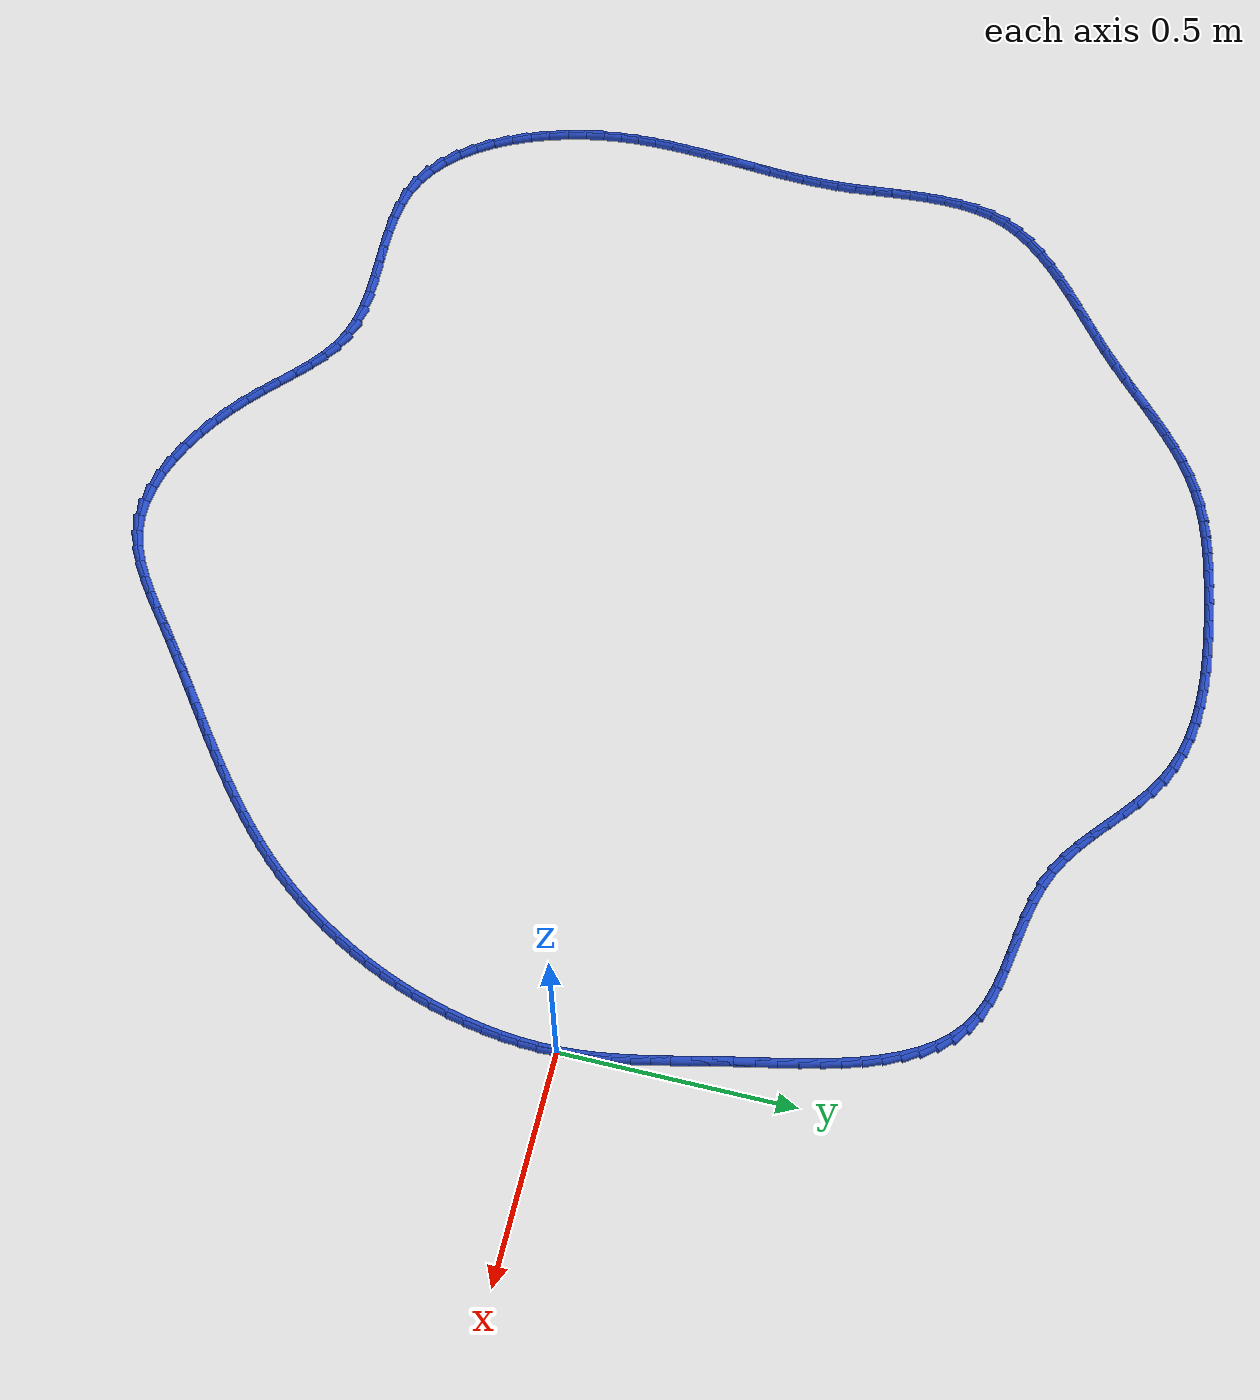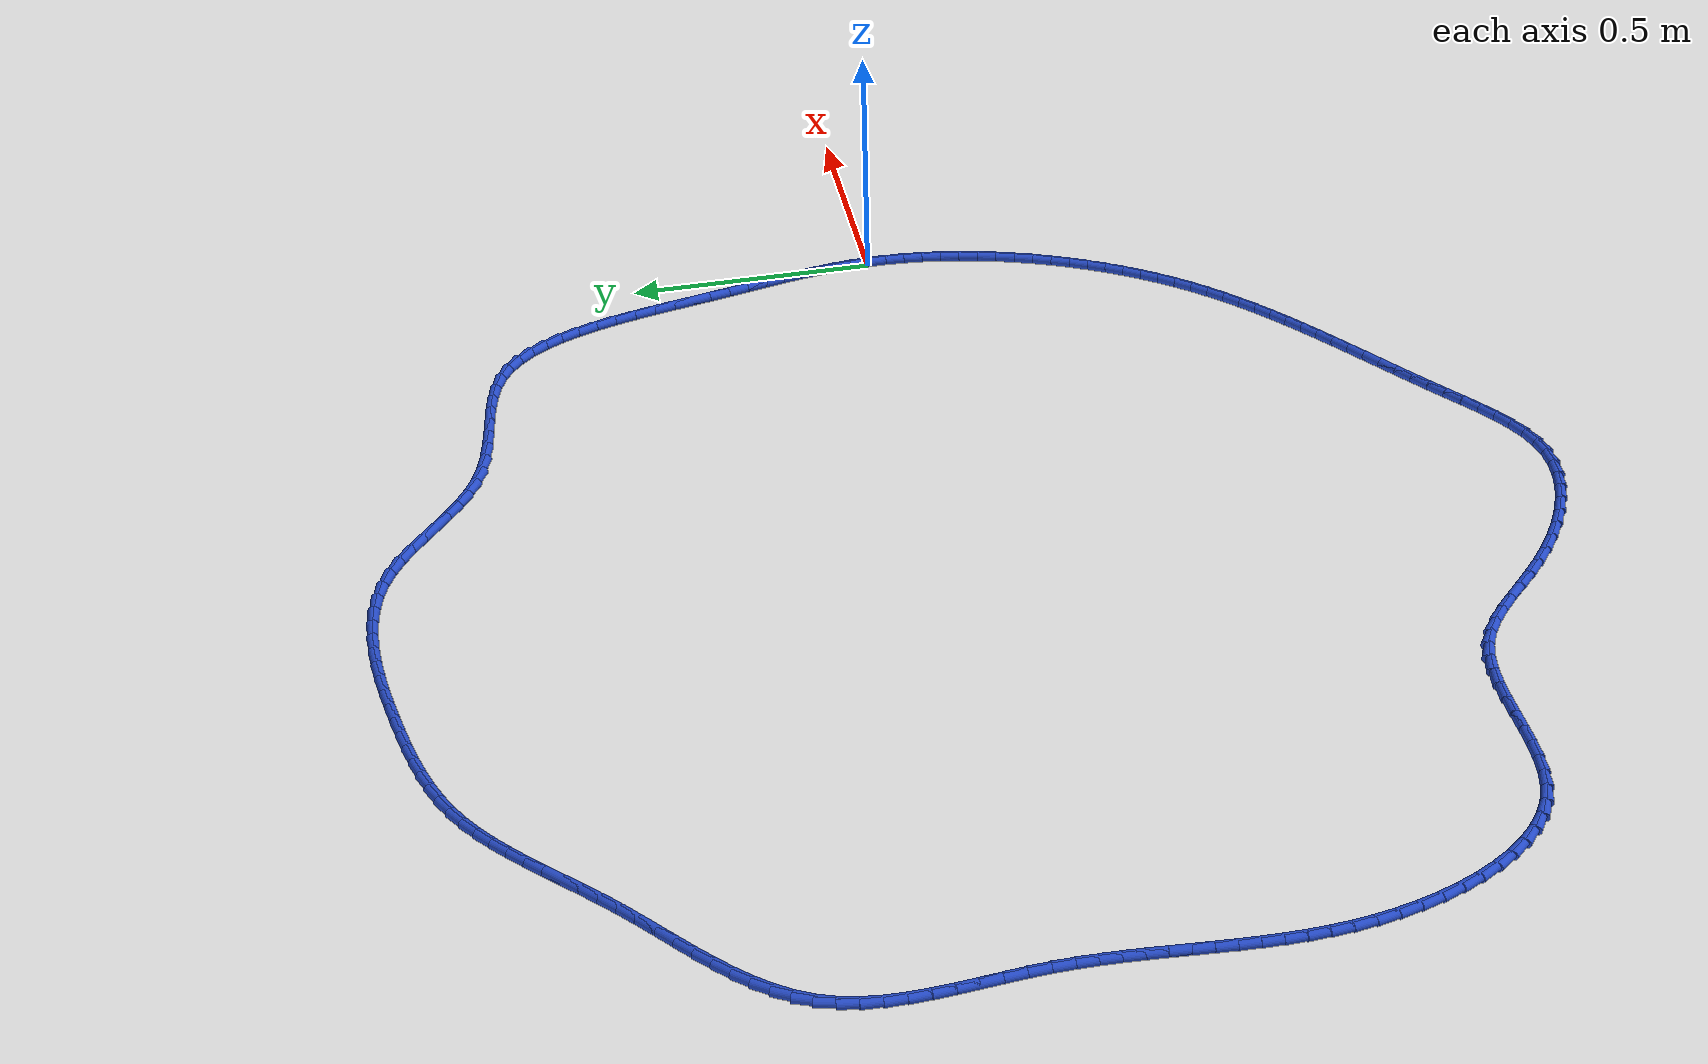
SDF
<sdf version="1.6">
 <world name="default">
  <light name="sun" type="directional">
   <pose>0 0 10 0 -0 0</pose>
   <diffuse>0.8 0.8 0.8 1</diffuse>
   <specular>0.2 0.2 0.2 1</specular>
   <attenuation>
    <range>1000</range>
    <constant>0.9</constant>
    <linear>0.01</linear>
    <quadratic>0.001</quadratic>
   </attenuation>
   <direction>-0.5 0.1 -0.9</direction>
  </light>
  <model name="ground_plane">
   <static>1</static>
   <link name="link">
    <collision name="collision">
     <geometry><plane><normal>0 0 1</normal><size>100 100</size></plane></geometry>
     <surface><friction><ode><mu>100</mu><mu2>50</mu2></ode></friction></surface>
    </collision>
    <visual name="visual">
     <cast_shadows>0</cast_shadows>
     <geometry><plane><normal>0 0 1</normal><size>100 100</size></plane></geometry>
     <material>
      <script><uri>file://media/materials/scripts/gazebo.material</uri><name>Gazebo/WhiteGlow</name></script>
     </material>
    </visual>
   </link>
  </model>
  <gravity>0 0 -9.8</gravity>
  <magnetic_field>6e-06 2.3e-05 -4.2e-05</magnetic_field>
  <atmosphere type="adiabatic"/>
  <physics name="default_physics" default="0" type="ode">
   <max_step_size>0.001</max_step_size>
   <real_time_factor>1</real_time_factor>
   <real_time_update_rate>1000</real_time_update_rate>
  </physics>
  <scene><ambient>0.4 0.4 0.4 1</ambient><background>0.7 0.7 0.7 1</background><shadows>1</shadows></scene>
  <spherical_coordinates>
   <surface_model>EARTH_WGS84</surface_model>
   <latitude_deg>0</latitude_deg>
   <longitude_deg>0</longitude_deg>
   <elevation>0</elevation>
   <heading_deg>0</heading_deg>
  </spherical_coordinates>
  <model name="line">
   <link name="link_0">
    <pose>-1.734723475976807e-17 -8.326672684688674e-17 0.01 0 1.57 -1.513674692497437</pose>
    <collision name="collision">
     <geometry><cylinder><radius>0.01</radius><length>0.08</length></cylinder></geometry>
    </collision>
    <visual name="visual">
     <material>
      <script><name>Gazebo/Blue</name><uri>file://media/materials/scripts/gazebo.material</uri></script>
     </material>
     <geometry><cylinder><radius>0.01</radius><length>0.08</length></cylinder></geometry>
    </visual>
   </link>
   <link name="link_1">
    <pose>-0.0021709766729972606 0.03796486170194264 0.01 0 1.57 -1.4669972326870937</pose>
    <collision name="collision">
     <geometry><cylinder><radius>0.01</radius><length>0.08</length></cylinder></geometry>
    </collision>
    <visual name="visual">
     <material>
      <script><name>Gazebo/Blue</name><uri>file://media/materials/scripts/gazebo.material</uri></script>
     </material>
     <geometry><cylinder><radius>0.01</radius><length>0.08</length></cylinder></geometry>
    </visual>
   </link>
   <link name="link_2">
    <pose>-0.006098873566817698 0.07567020072753589 0.01 0 1.57 -1.4274373858013119</pose>
    <collision name="collision">
     <geometry><cylinder><radius>0.01</radius><length>0.08</length></cylinder></geometry>
    </collision>
    <visual name="visual">
     <material>
      <script><name>Gazebo/Blue</name><uri>file://media/materials/scripts/gazebo.material</uri></script>
     </material>
     <geometry><cylinder><radius>0.01</radius><length>0.08</length></cylinder></geometry>
    </visual>
   </link>
   <link name="link_3">
    <pose>-0.011529944591555437 0.1132947384150805 0.01 0 1.57 -1.395517599907526</pose>
    <collision name="collision">
     <geometry><cylinder><radius>0.01</radius><length>0.08</length></cylinder></geometry>
    </collision>
    <visual name="visual">
     <material>
      <script><name>Gazebo/Blue</name><uri>file://media/materials/scripts/gazebo.material</uri></script>
     </material>
     <geometry><cylinder><radius>0.01</radius><length>0.08</length></cylinder></geometry>
    </visual>
   </link>
   <link name="link_4">
    <pose>-0.018210443657304606 0.1510171961028775 0.01 0 1.57 -1.3714692530804347</pose>
    <collision name="collision">
     <geometry><cylinder><radius>0.01</radius><length>0.08</length></cylinder></geometry>
    </collision>
    <visual name="visual">
     <material>
      <script><name>Gazebo/Blue</name><uri>file://media/materials/scripts/gazebo.material</uri></script>
     </material>
     <geometry><cylinder><radius>0.01</radius><length>0.08</length></cylinder></geometry>
    </visual>
   </link>
   <link name="link_5">
    <pose>-0.025886624674159295 0.18901629512922768 0.01 0 1.57 -1.3552846814943524</pose>
    <collision name="collision">
     <geometry><cylinder><radius>0.01</radius><length>0.08</length></cylinder></geometry>
    </collision>
    <visual name="visual">
     <material>
      <script><name>Gazebo/Blue</name><uri>file://media/materials/scripts/gazebo.material</uri></script>
     </material>
     <geometry><cylinder><radius>0.01</radius><length>0.08</length></cylinder></geometry>
    </visual>
   </link>
   <link name="link_6">
    <pose>-0.034304741552213636 0.227470756832432 0.01 0 1.57 -1.3467713244768782</pose>
    <collision name="collision">
     <geometry><cylinder><radius>0.01</radius><length>0.08</length></cylinder></geometry>
    </collision>
    <visual name="visual">
     <material>
      <script><name>Gazebo/Blue</name><uri>file://media/materials/scripts/gazebo.material</uri></script>
     </material>
     <geometry><cylinder><radius>0.01</radius><length>0.08</length></cylinder></geometry>
    </visual>
   </link>
   <link name="link_7">
    <pose>-0.043211048201561734 0.2665593025507914 0.01 0 1.57 -1.3455983475022786</pose>
    <collision name="collision">
     <geometry><cylinder><radius>0.01</radius><length>0.08</length></cylinder></geometry>
    </collision>
    <visual name="visual">
     <material>
      <script><name>Gazebo/Blue</name><uri>file://media/materials/scripts/gazebo.material</uri></script>
     </material>
     <geometry><cylinder><radius>0.01</radius><length>0.08</length></cylinder></geometry>
    </visual>
   </link>
   <link name="link_8">
    <pose>-0.0523517985322977 0.30646065362260666 0.01 0 1.57 -1.3513260966886542</pose>
    <collision name="collision">
     <geometry><cylinder><radius>0.01</radius><length>0.08</length></cylinder></geometry>
    </collision>
    <visual name="visual">
     <material>
      <script><name>Gazebo/Blue</name><uri>file://media/materials/scripts/gazebo.material</uri></script>
     </material>
     <geometry><cylinder><radius>0.01</radius><length>0.08</length></cylinder></geometry>
    </visual>
   </link>
   <link name="link_9">
    <pose>-0.0614734442344838 0.34735330036969936 0.01 0 1.57 -1.3596868621328406</pose>
    <collision name="collision">
     <geometry><cylinder><radius>0.01</radius><length>0.08</length></cylinder></geometry>
    </collision>
    <visual name="visual">
     <material>
      <script><name>Gazebo/Blue</name><uri>file://media/materials/scripts/gazebo.material</uri></script>
     </material>
     <geometry><cylinder><radius>0.01</radius><length>0.08</length></cylinder></geometry>
    </visual>
   </link>
   <link name="link_10">
    <pose>-0.07045447994527271 0.38926150062493287 0.01 0 1.57 -1.360450521284114</pose>
    <collision name="collision">
     <geometry><cylinder><radius>0.01</radius><length>0.08</length></cylinder></geometry>
    </collision>
    <visual name="visual">
     <material>
      <script><name>Gazebo/Blue</name><uri>file://media/materials/scripts/gazebo.material</uri></script>
     </material>
     <geometry><cylinder><radius>0.01</radius><length>0.08</length></cylinder></geometry>
    </visual>
   </link>
   <link name="link_11">
    <pose>-0.07953409943745247 0.4317881983480699 0.01 0 1.57 -1.3522462127064545</pose>
    <collision name="collision">
     <geometry><cylinder><radius>0.01</radius><length>0.08</length></cylinder></geometry>
    </collision>
    <visual name="visual">
     <material>
      <script><name>Gazebo/Blue</name><uri>file://media/materials/scripts/gazebo.material</uri></script>
     </material>
     <geometry><cylinder><radius>0.01</radius><length>0.08</length></cylinder></geometry>
    </visual>
   </link>
   <link name="link_12">
    <pose>-0.08901252365885924 0.4744650548343381 0.01 0 1.57 -1.3349976137823825</pose>
    <collision name="collision">
     <geometry><cylinder><radius>0.01</radius><length>0.08</length></cylinder></geometry>
    </collision>
    <visual name="visual">
     <material>
      <script><name>Gazebo/Blue</name><uri>file://media/materials/scripts/gazebo.material</uri></script>
     </material>
     <geometry><cylinder><radius>0.01</radius><length>0.08</length></cylinder></geometry>
    </visual>
   </link>
   <link name="link_13">
    <pose>-0.09918997355732917 0.5168237313789648 0.01 0 1.57 -1.308156172855228</pose>
    <collision name="collision">
     <geometry><cylinder><radius>0.01</radius><length>0.08</length></cylinder></geometry>
    </collision>
    <visual name="visual">
     <material>
      <script><name>Gazebo/Blue</name><uri>file://media/materials/scripts/gazebo.material</uri></script>
     </material>
     <geometry><cylinder><radius>0.01</radius><length>0.08</length></cylinder></geometry>
    </visual>
   </link>
   <link name="link_14">
    <pose>-0.11036667008069828 0.5583958892771769 0.01 0 1.57 -1.2706930697005803</pose>
    <collision name="collision">
     <geometry><cylinder><radius>0.01</radius><length>0.08</length></cylinder></geometry>
    </collision>
    <visual name="visual">
     <material>
      <script><name>Gazebo/Blue</name><uri>file://media/materials/scripts/gazebo.material</uri></script>
     </material>
     <geometry><cylinder><radius>0.01</radius><length>0.08</length></cylinder></geometry>
    </visual>
   </link>
   <link name="link_15">
    <pose>-0.1228428341768028 0.5987131898242023 0.01 0 1.57 -1.2210729023385336</pose>
    <collision name="collision">
     <geometry><cylinder><radius>0.01</radius><length>0.08</length></cylinder></geometry>
    </collision>
    <visual name="visual">
     <material>
      <script><name>Gazebo/Blue</name><uri>file://media/materials/scripts/gazebo.material</uri></script>
     </material>
     <geometry><cylinder><radius>0.01</radius><length>0.08</length></cylinder></geometry>
    </visual>
   </link>
   <link name="link_16">
    <pose>-0.13691868679347874 0.6373072943152678 0.01 0 1.57 -1.157241945169081</pose>
    <collision name="collision">
     <geometry><cylinder><radius>0.01</radius><length>0.08</length></cylinder></geometry>
    </collision>
    <visual name="visual">
     <material>
      <script><name>Gazebo/Blue</name><uri>file://media/materials/scripts/gazebo.material</uri></script>
     </material>
     <geometry><cylinder><radius>0.01</radius><length>0.08</length></cylinder></geometry>
    </visual>
   </link>
   <link name="link_17">
    <pose>-0.15289444887856227 0.6737098640456011 0.01 0 1.57 -1.0766999290949455</pose>
    <collision name="collision">
     <geometry><cylinder><radius>0.01</radius><length>0.08</length></cylinder></geometry>
    </collision>
    <visual name="visual">
     <material>
      <script><name>Gazebo/Blue</name><uri>file://media/materials/scripts/gazebo.material</uri></script>
     </material>
     <geometry><cylinder><radius>0.01</radius><length>0.08</length></cylinder></geometry>
    </visual>
   </link>
   <link name="link_18">
    <pose>-0.17107034137988955 0.7074525603104292 0.01 0 1.57 -0.9767893826048268</pose>
    <collision name="collision">
     <geometry><cylinder><radius>0.01</radius><length>0.08</length></cylinder></geometry>
    </collision>
    <visual name="visual">
     <material>
      <script><name>Gazebo/Blue</name><uri>file://media/materials/scripts/gazebo.material</uri></script>
     </material>
     <geometry><cylinder><radius>0.01</radius><length>0.08</length></cylinder></geometry>
    </visual>
   </link>
   <link name="link_19">
    <pose>-0.19174658524529664 0.7380670444049798 0.01 0 1.57 -0.8554119586579254</pose>
    <collision name="collision">
     <geometry><cylinder><radius>0.01</radius><length>0.08</length></cylinder></geometry>
    </collision>
    <visual name="visual">
     <material>
      <script><name>Gazebo/Blue</name><uri>file://media/materials/scripts/gazebo.material</uri></script>
     </material>
     <geometry><cylinder><radius>0.01</radius><length>0.08</length></cylinder></geometry>
    </visual>
   </link>
   <link name="link_20">
    <pose>-0.21522340142261973 0.7650849776244799 0.01 0 1.57 -0.7123501342250036</pose>
    <collision name="collision">
     <geometry><cylinder><radius>0.01</radius><length>0.08</length></cylinder></geometry>
    </collision>
    <visual name="visual">
     <material>
      <script><name>Gazebo/Blue</name><uri>file://media/materials/scripts/gazebo.material</uri></script>
     </material>
     <geometry><cylinder><radius>0.01</radius><length>0.08</length></cylinder></geometry>
    </visual>
   </link>
   <link name="link_21">
    <pose>-0.2418010108596948 0.7880380212641569 0.01 0 1.57 -0.5512669641992515</pose>
    <collision name="collision">
     <geometry><cylinder><radius>0.01</radius><length>0.08</length></cylinder></geometry>
    </collision>
    <visual name="visual">
     <material>
      <script><name>Gazebo/Blue</name><uri>file://media/materials/scripts/gazebo.material</uri></script>
     </material>
     <geometry><cylinder><radius>0.01</radius><length>0.08</length></cylinder></geometry>
    </visual>
   </link>
   <link name="link_22">
    <pose>-0.2717738640512207 0.8064668235413669 0.01 0 1.57 -0.39767166093975875</pose>
    <collision name="collision">
     <geometry><cylinder><radius>0.01</radius><length>0.08</length></cylinder></geometry>
    </collision>
    <visual name="visual">
     <material>
      <script><name>Gazebo/Blue</name><uri>file://media/materials/scripts/gazebo.material</uri></script>
     </material>
     <geometry><cylinder><radius>0.01</radius><length>0.08</length></cylinder></geometry>
    </visual>
   </link>
   <link name="link_23">
    <pose>-0.30508505567657657 0.8204592353413556 0.01 0 1.57 -0.2833727117920322</pose>
    <collision name="collision">
     <geometry><cylinder><radius>0.01</radius><length>0.08</length></cylinder></geometry>
    </collision>
    <visual name="visual">
     <material>
      <script><name>Gazebo/Blue</name><uri>file://media/materials/scripts/gazebo.material</uri></script>
     </material>
     <geometry><cylinder><radius>0.01</radius><length>0.08</length></cylinder></geometry>
    </visual>
   </link>
   <link name="link_24">
    <pose>-0.3411301092904989 0.8309558965660844 0.01 0 1.57 -0.20721285598285735</pose>
    <collision name="collision">
     <geometry><cylinder><radius>0.01</radius><length>0.08</length></cylinder></geometry>
    </collision>
    <visual name="visual">
     <material>
      <script><name>Gazebo/Blue</name><uri>file://media/materials/scripts/gazebo.material</uri></script>
     </material>
     <geometry><cylinder><radius>0.01</radius><length>0.08</length></cylinder></geometry>
    </visual>
   </link>
   <link name="link_25">
    <pose>-0.3792570967580207 0.8389713485304704 0.01 0 1.57 -0.16406504067815078</pose>
    <collision name="collision">
     <geometry><cylinder><radius>0.01</radius><length>0.08</length></cylinder></geometry>
    </collision>
    <visual name="visual">
     <material>
      <script><name>Gazebo/Blue</name><uri>file://media/materials/scripts/gazebo.material</uri></script>
     </material>
     <geometry><cylinder><radius>0.01</radius><length>0.08</length></cylinder></geometry>
    </visual>
   </link>
   <link name="link_26">
    <pose>-0.4188140899441745 0.8455201325494298 0.01 0 1.57 -0.15001472913109795</pose>
    <collision name="collision">
     <geometry><cylinder><radius>0.01</radius><length>0.08</length></cylinder></geometry>
    </collision>
    <visual name="visual">
     <material>
      <script><name>Gazebo/Blue</name><uri>file://media/materials/scripts/gazebo.material</uri></script>
     </material>
     <geometry><cylinder><radius>0.01</radius><length>0.08</length></cylinder></geometry>
    </visual>
   </link>
   <link name="link_27">
    <pose>-0.4591491607139927 0.851616789937879 0.01 0 1.57 -0.16311686723959543</pose>
    <collision name="collision">
     <geometry><cylinder><radius>0.01</radius><length>0.08</length></cylinder></geometry>
    </collision>
    <visual name="visual">
     <material>
      <script><name>Gazebo/Blue</name><uri>file://media/materials/scripts/gazebo.material</uri></script>
     </material>
     <geometry><cylinder><radius>0.01</radius><length>0.08</length></cylinder></geometry>
    </visual>
   </link>
   <link name="link_28">
    <pose>-0.49961038093250837 0.8582758620107347 0.01 0 1.57 -0.2033821145523766</pose>
    <collision name="collision">
     <geometry><cylinder><radius>0.01</radius><length>0.08</length></cylinder></geometry>
    </collision>
    <visual name="visual">
     <material>
      <script><name>Gazebo/Blue</name><uri>file://media/materials/scripts/gazebo.material</uri></script>
     </material>
     <geometry><cylinder><radius>0.01</radius><length>0.08</length></cylinder></geometry>
    </visual>
   </link>
   <link name="link_29">
    <pose>-0.5395458224647537 0.866511890082913 0.01 0 1.57 -0.2724190725787094</pose>
    <collision name="collision">
     <geometry><cylinder><radius>0.01</radius><length>0.08</length></cylinder></geometry>
    </collision>
    <visual name="visual">
     <material>
      <script><name>Gazebo/Blue</name><uri>file://media/materials/scripts/gazebo.material</uri></script>
     </material>
     <geometry><cylinder><radius>0.01</radius><length>0.08</length></cylinder></geometry>
    </visual>
   </link>
   <link name="link_30">
    <pose>-0.5783035571757615 0.8773394154693307 0.01 0 1.57 -0.37254192159076943</pose>
    <collision name="collision">
     <geometry><cylinder><radius>0.01</radius><length>0.08</length></cylinder></geometry>
    </collision>
    <visual name="visual">
     <material>
      <script><name>Gazebo/Blue</name><uri>file://media/materials/scripts/gazebo.material</uri></script>
     </material>
     <geometry><cylinder><radius>0.01</radius><length>0.08</length></cylinder></geometry>
    </visual>
   </link>
   <link name="link_31">
    <pose>-0.6152327723834674 0.891770997392256 0.01 0 1.57 -0.4891496441528137</pose>
    <collision name="collision">
     <geometry><cylinder><radius>0.01</radius><length>0.08</length></cylinder></geometry>
    </collision>
    <visual name="visual">
     <material>
      <script><name>Gazebo/Blue</name><uri>file://media/materials/scripts/gazebo.material</uri></script>
     </material>
     <geometry><cylinder><radius>0.01</radius><length>0.08</length></cylinder></geometry>
    </visual>
   </link>
   <link name="link_32">
    <pose>-0.6499903980548309 0.9102723549155197 0.01 0 1.57 -0.5831332911938399</pose>
    <collision name="collision">
     <geometry><cylinder><radius>0.01</radius><length>0.08</length></cylinder></geometry>
    </collision>
    <visual name="visual">
     <material>
      <script><name>Gazebo/Blue</name><uri>file://media/materials/scripts/gazebo.material</uri></script>
     </material>
     <geometry><cylinder><radius>0.01</radius><length>0.08</length></cylinder></geometry>
    </visual>
   </link>
   <link name="link_33">
    <pose>-0.6829587979100286 0.9320201550011309 0.01 0 1.57 -0.6482492501307774</pose>
    <collision name="collision">
     <geometry><cylinder><radius>0.01</radius><length>0.08</length></cylinder></geometry>
    </collision>
    <visual name="visual">
     <material>
      <script><name>Gazebo/Blue</name><uri>file://media/materials/scripts/gazebo.material</uri></script>
     </material>
     <geometry><cylinder><radius>0.01</radius><length>0.08</length></cylinder></geometry>
    </visual>
   </link>
   <link name="link_34">
    <pose>-0.7146248042198272 0.9560054302866448 0.01 0 1.57 -0.6851955144747639</pose>
    <collision name="collision">
     <geometry><cylinder><radius>0.01</radius><length>0.08</length></cylinder></geometry>
    </collision>
    <visual name="visual">
     <material>
      <script><name>Gazebo/Blue</name><uri>file://media/materials/scripts/gazebo.material</uri></script>
     </material>
     <geometry><cylinder><radius>0.01</radius><length>0.08</length></cylinder></geometry>
    </visual>
   </link>
   <link name="link_35">
    <pose>-0.7454752492549945 0.9812192134096167 0.01 0 1.57 -0.6947104365108867</pose>
    <collision name="collision">
     <geometry><cylinder><radius>0.01</radius><length>0.08</length></cylinder></geometry>
    </collision>
    <visual name="visual">
     <material>
      <script><name>Gazebo/Blue</name><uri>file://media/materials/scripts/gazebo.material</uri></script>
     </material>
     <geometry><cylinder><radius>0.01</radius><length>0.08</length></cylinder></geometry>
    </visual>
   </link>
   <link name="link_36">
    <pose>-0.775996965286298 1.0066525370076025 0.01 0 1.57 -0.6767260849222654</pose>
    <collision name="collision">
     <geometry><cylinder><radius>0.01</radius><length>0.08</length></cylinder></geometry>
    </collision>
    <visual name="visual">
     <material>
      <script><name>Gazebo/Blue</name><uri>file://media/materials/scripts/gazebo.material</uri></script>
     </material>
     <geometry><cylinder><radius>0.01</radius><length>0.08</length></cylinder></geometry>
    </visual>
   </link>
   <link name="link_37">
    <pose>-0.8066767845845049 1.0312964337181578 0.01 0 1.57 -0.6301284305034272</pose>
    <collision name="collision">
     <geometry><cylinder><radius>0.01</radius><length>0.08</length></cylinder></geometry>
    </collision>
    <visual name="visual">
     <material>
      <script><name>Gazebo/Blue</name><uri>file://media/materials/scripts/gazebo.material</uri></script>
     </material>
     <geometry><cylinder><radius>0.01</radius><length>0.08</length></cylinder></geometry>
    </visual>
   </link>
   <link name="link_38">
    <pose>-0.8380015394203821 1.0541419361788373 0.01 0 1.57 -0.5531039544266814</pose>
    <collision name="collision">
     <geometry><cylinder><radius>0.01</radius><length>0.08</length></cylinder></geometry>
    </collision>
    <visual name="visual">
     <material>
      <script><name>Gazebo/Blue</name><uri>file://media/materials/scripts/gazebo.material</uri></script>
     </material>
     <geometry><cylinder><radius>0.01</radius><length>0.08</length></cylinder></geometry>
    </visual>
   </link>
   <link name="link_39">
    <pose>-0.870458062064698 1.0741800770271976 0.01 0 1.57 -0.4468984612108868</pose>
    <collision name="collision">
     <geometry><cylinder><radius>0.01</radius><length>0.08</length></cylinder></geometry>
    </collision>
    <visual name="visual">
     <material>
      <script><name>Gazebo/Blue</name><uri>file://media/materials/scripts/gazebo.material</uri></script>
     </material>
     <geometry><cylinder><radius>0.01</radius><length>0.08</length></cylinder></geometry>
    </visual>
   </link>
   <link name="link_40">
    <pose>-0.9044886577543308 1.0904887471534044 0.01 0 1.57 -0.3366890647242131</pose>
    <collision name="collision">
     <geometry><cylinder><radius>0.01</radius><length>0.08</length></cylinder></geometry>
    </collision>
    <visual name="visual">
     <material>
      <script><name>Gazebo/Blue</name><uri>file://media/materials/scripts/gazebo.material</uri></script>
     </material>
     <geometry><cylinder><radius>0.01</radius><length>0.08</length></cylinder></geometry>
    </visual>
   </link>
   <link name="link_41">
    <pose>-0.9401183994672703 1.1029597264892868 0.01 0 1.57 -0.2376840402317538</pose>
    <collision name="collision">
     <geometry><cylinder><radius>0.01</radius><length>0.08</length></cylinder></geometry>
    </collision>
    <visual name="visual">
     <material>
      <script><name>Gazebo/Blue</name><uri>file://media/materials/scripts/gazebo.material</uri></script>
     </material>
     <geometry><cylinder><radius>0.01</radius><length>0.08</length></cylinder></geometry>
    </visual>
   </link>
   <link name="link_42">
    <pose>-0.9771442636998153 1.1119297395339647 0.01 0 1.57 -0.15088027971425613</pose>
    <collision name="collision">
     <geometry><cylinder><radius>0.01</radius><length>0.08</length></cylinder></geometry>
    </collision>
    <visual name="visual">
     <material>
      <script><name>Gazebo/Blue</name><uri>file://media/materials/scripts/gazebo.material</uri></script>
     </material>
     <geometry><cylinder><radius>0.01</radius><length>0.08</length></cylinder></geometry>
    </visual>
   </link>
   <link name="link_43">
    <pose>-1.0153609077943728 1.117740034727116 0.01 0 1.57 -0.07617037986373879</pose>
    <collision name="collision">
     <geometry><cylinder><radius>0.01</radius><length>0.08</length></cylinder></geometry>
    </collision>
    <visual name="visual">
     <material>
      <script><name>Gazebo/Blue</name><uri>file://media/materials/scripts/gazebo.material</uri></script>
     </material>
     <geometry><cylinder><radius>0.01</radius><length>0.08</length></cylinder></geometry>
    </visual>
   </link>
   <link name="link_44">
    <pose>-1.054562989093351 1.120731860508417 0.01 0 1.57 -0.012870144877667853</pose>
    <collision name="collision">
     <geometry><cylinder><radius>0.01</radius><length>0.08</length></cylinder></geometry>
    </collision>
    <visual name="visual">
     <material>
      <script><name>Gazebo/Blue</name><uri>file://media/materials/scripts/gazebo.material</uri></script>
     </material>
     <geometry><cylinder><radius>0.01</radius><length>0.08</length></cylinder></geometry>
    </visual>
   </link>
   <link name="link_45">
    <pose>-1.0945451649391567 1.1212464653175456 0.01 0 1.57 0.03995630046324833</pose>
    <collision name="collision">
     <geometry><cylinder><radius>0.01</radius><length>0.08</length></cylinder></geometry>
    </collision>
    <visual name="visual">
     <material>
      <script><name>Gazebo/Blue</name><uri>file://media/materials/scripts/gazebo.material</uri></script>
     </material>
     <geometry><cylinder><radius>0.01</radius><length>0.08</length></cylinder></geometry>
    </visual>
   </link>
   <link name="link_46">
    <pose>-1.1351020926741977 1.119625097594178 0.01 0 1.57 0.08327623793226487</pose>
    <collision name="collision">
     <geometry><cylinder><radius>0.01</radius><length>0.08</length></cylinder></geometry>
    </collision>
    <visual name="visual">
     <material>
      <script><name>Gazebo/Blue</name><uri>file://media/materials/scripts/gazebo.material</uri></script>
     </material>
     <geometry><cylinder><radius>0.01</radius><length>0.08</length></cylinder></geometry>
    </visual>
   </link>
   <link name="link_47">
    <pose>-1.1760284296408814 1.1162090057779916 0.01 0 1.57 0.11795846947127982</pose>
    <collision name="collision">
     <geometry><cylinder><radius>0.01</radius><length>0.08</length></cylinder></geometry>
    </collision>
    <visual name="visual">
     <material>
      <script><name>Gazebo/Blue</name><uri>file://media/materials/scripts/gazebo.material</uri></script>
     </material>
     <geometry><cylinder><radius>0.01</radius><length>0.08</length></cylinder></geometry>
    </visual>
   </link>
   <link name="link_48">
    <pose>-1.2171188331816152 1.1113394383086634 0.01 0 1.57 0.14470428627917575</pose>
    <collision name="collision">
     <geometry><cylinder><radius>0.01</radius><length>0.08</length></cylinder></geometry>
    </collision>
    <visual name="visual">
     <material>
      <script><name>Gazebo/Blue</name><uri>file://media/materials/scripts/gazebo.material</uri></script>
     </material>
     <geometry><cylinder><radius>0.01</radius><length>0.08</length></cylinder></geometry>
    </visual>
   </link>
   <link name="link_49">
    <pose>-1.2581679606388074 1.105357643625871 0.01 0 1.57 0.16401233236463345</pose>
    <collision name="collision">
     <geometry><cylinder><radius>0.01</radius><length>0.08</length></cylinder></geometry>
    </collision>
    <visual name="visual">
     <material>
      <script><name>Gazebo/Blue</name><uri>file://media/materials/scripts/gazebo.material</uri></script>
     </material>
     <geometry><cylinder><radius>0.01</radius><length>0.08</length></cylinder></geometry>
    </visual>
   </link>
   <link name="link_50">
    <pose>-1.2989704693548645 1.098604870169291 0.01 0 1.57 0.17802899333277394</pose>
    <collision name="collision">
     <geometry><cylinder><radius>0.01</radius><length>0.08</length></cylinder></geometry>
    </collision>
    <visual name="visual">
     <material>
      <script><name>Gazebo/Blue</name><uri>file://media/materials/scripts/gazebo.material</uri></script>
     </material>
     <geometry><cylinder><radius>0.01</radius><length>0.08</length></cylinder></geometry>
    </visual>
   </link>
   <link name="link_51">
    <pose>-1.3393264413347388 1.0913434593508782 0.01 0 1.57 0.19718736685031807</pose>
    <collision name="collision">
     <geometry><cylinder><radius>0.01</radius><length>0.08</length></cylinder></geometry>
    </collision>
    <visual name="visual">
     <material>
      <script><name>Gazebo/Blue</name><uri>file://media/materials/scripts/gazebo.material</uri></script>
     </material>
     <geometry><cylinder><radius>0.01</radius><length>0.08</length></cylinder></geometry>
    </visual>
   </link>
   <link name="link_52">
    <pose>-1.379065624922745 1.0834042266317674 0.01 0 1.57 0.22537833955243236</pose>
    <collision name="collision">
     <geometry><cylinder><radius>0.01</radius><length>0.08</length></cylinder></geometry>
    </collision>
    <visual name="visual">
     <material>
      <script><name>Gazebo/Blue</name><uri>file://media/materials/scripts/gazebo.material</uri></script>
     </material>
     <geometry><cylinder><radius>0.01</radius><length>0.08</length></cylinder></geometry>
    </visual>
   </link>
   <link name="link_53">
    <pose>-1.4180278586046946 1.0744712164862766 0.01 0 1.57 0.2631254187880046</pose>
    <collision name="collision">
     <geometry><cylinder><radius>0.01</radius><length>0.08</length></cylinder></geometry>
    </collision>
    <visual name="visual">
     <material>
      <script><name>Gazebo/Blue</name><uri>file://media/materials/scripts/gazebo.material</uri></script>
     </material>
     <geometry><cylinder><radius>0.01</radius><length>0.08</length></cylinder></geometry>
    </visual>
   </link>
   <link name="link_54">
    <pose>-1.4560529892442529 1.0642283515246327 0.01 0 1.57 0.3109767610904056</pose>
    <collision name="collision">
     <geometry><cylinder><radius>0.01</radius><length>0.08</length></cylinder></geometry>
    </collision>
    <visual name="visual">
     <material>
      <script><name>Gazebo/Blue</name><uri>file://media/materials/scripts/gazebo.material</uri></script>
     </material>
     <geometry><cylinder><radius>0.01</radius><length>0.08</length></cylinder></geometry>
    </visual>
   </link>
   <link name="link_55">
    <pose>-1.4929808637050854 1.052359554357063 0.01 0 1.57 0.36940398950234254</pose>
    <collision name="collision">
     <geometry><cylinder><radius>0.01</radius><length>0.08</length></cylinder></geometry>
    </collision>
    <visual name="visual">
     <material>
      <script><name>Gazebo/Blue</name><uri>file://media/materials/scripts/gazebo.material</uri></script>
     </material>
     <geometry><cylinder><radius>0.01</radius><length>0.08</length></cylinder></geometry>
    </visual>
   </link>
   <link name="link_56">
    <pose>-1.5286513288508574 1.0385487475937936 0.01 0 1.57 0.43864397998230575</pose>
    <collision name="collision">
     <geometry><cylinder><radius>0.01</radius><length>0.08</length></cylinder></geometry>
    </collision>
    <visual name="visual">
     <material>
      <script><name>Gazebo/Blue</name><uri>file://media/materials/scripts/gazebo.material</uri></script>
     </material>
     <geometry><cylinder><radius>0.01</radius><length>0.08</length></cylinder></geometry>
    </visual>
   </link>
   <link name="link_57">
    <pose>-1.5629042315452353 1.0224798538450526 0.01 0 1.57 0.5167463792292899</pose>
    <collision name="collision">
     <geometry><cylinder><radius>0.01</radius><length>0.08</length></cylinder></geometry>
    </collision>
    <visual name="visual">
     <material>
      <script><name>Gazebo/Blue</name><uri>file://media/materials/scripts/gazebo.material</uri></script>
     </material>
     <geometry><cylinder><radius>0.01</radius><length>0.08</length></cylinder></geometry>
    </visual>
   </link>
   <link name="link_58">
    <pose>-1.5956164377119544 1.0038911556902537 0.01 0 1.57 0.5896048283809276</pose>
    <collision name="collision">
     <geometry><cylinder><radius>0.01</radius><length>0.08</length></cylinder></geometry>
    </collision>
    <visual name="visual">
     <material>
      <script><name>Gazebo/Blue</name><uri>file://media/materials/scripts/gazebo.material</uri></script>
     </material>
     <geometry><cylinder><radius>0.01</radius><length>0.08</length></cylinder></geometry>
    </visual>
   </link>
   <link name="link_59">
    <pose>-1.626945231402158 0.9829327106360024 0.01 0 1.57 0.6501632352882499</pose>
    <collision name="collision">
     <geometry><cylinder><radius>0.01</radius><length>0.08</length></cylinder></geometry>
    </collision>
    <visual name="visual">
     <material>
      <script><name>Gazebo/Blue</name><uri>file://media/materials/scripts/gazebo.material</uri></script>
     </material>
     <geometry><cylinder><radius>0.01</radius><length>0.08</length></cylinder></geometry>
    </visual>
   </link>
   <link name="link_60">
    <pose>-1.6571763017732026 0.9599431303446265 0.01 0 1.57 0.6980332330648967</pose>
    <collision name="collision">
     <geometry><cylinder><radius>0.01</radius><length>0.08</length></cylinder></geometry>
    </collision>
    <visual name="visual">
     <material>
      <script><name>Gazebo/Blue</name><uri>file://media/materials/scripts/gazebo.material</uri></script>
     </material>
     <geometry><cylinder><radius>0.01</radius><length>0.08</length></cylinder></geometry>
    </visual>
   </link>
   <link name="link_61">
    <pose>-1.6865960043152728 0.935262004942843 0.01 0 1.57 0.7333475334357399</pose>
    <collision name="collision">
     <geometry><cylinder><radius>0.01</radius><length>0.08</length></cylinder></geometry>
    </collision>
    <visual name="visual">
     <material>
      <script><name>Gazebo/Blue</name><uri>file://media/materials/scripts/gazebo.material</uri></script>
     </material>
     <geometry><cylinder><radius>0.01</radius><length>0.08</length></cylinder></geometry>
    </visual>
   </link>
   <link name="link_62">
    <pose>-1.7154906945185526 0.9092289245573677 0.01 0 1.57 0.7564915790419889</pose>
    <collision name="collision">
     <geometry><cylinder><radius>0.01</radius><length>0.08</length></cylinder></geometry>
    </collision>
    <visual name="visual">
     <material>
      <script><name>Gazebo/Blue</name><uri>file://media/materials/scripts/gazebo.material</uri></script>
     </material>
     <geometry><cylinder><radius>0.01</radius><length>0.08</length></cylinder></geometry>
    </visual>
   </link>
   <link name="link_63">
    <pose>-1.7441467278732268 0.882183479314916 0.01 0 1.57 0.7679331203728142</pose>
    <collision name="collision">
     <geometry><cylinder><radius>0.01</radius><length>0.08</length></cylinder></geometry>
    </collision>
    <visual name="visual">
     <material>
      <script><name>Gazebo/Blue</name><uri>file://media/materials/scripts/gazebo.material</uri></script>
     </material>
     <geometry><cylinder><radius>0.01</radius><length>0.08</length></cylinder></geometry>
    </visual>
   </link>
   <link name="link_64">
    <pose>-1.7728504598694785 0.8544652593422049 0.01 0 1.57 0.7681219784722797</pose>
    <collision name="collision">
     <geometry><cylinder><radius>0.01</radius><length>0.08</length></cylinder></geometry>
    </collision>
    <visual name="visual">
     <material>
      <script><name>Gazebo/Blue</name><uri>file://media/materials/scripts/gazebo.material</uri></script>
     </material>
     <geometry><cylinder><radius>0.01</radius><length>0.08</length></cylinder></geometry>
    </visual>
   </link>
   <link name="link_65">
    <pose>-1.8018882459974925 0.8264138547659501 0.01 0 1.57 0.7574486431471186</pose>
    <collision name="collision">
     <geometry><cylinder><radius>0.01</radius><length>0.08</length></cylinder></geometry>
    </collision>
    <visual name="visual">
     <material>
      <script><name>Gazebo/Blue</name><uri>file://media/materials/scripts/gazebo.material</uri></script>
     </material>
     <geometry><cylinder><radius>0.01</radius><length>0.08</length></cylinder></geometry>
    </visual>
   </link>
   <link name="link_66">
    <pose>-1.8315464417474532 0.7983688557128671 0.01 0 1.57 0.7362486674125462</pose>
    <collision name="collision">
     <geometry><cylinder><radius>0.01</radius><length>0.08</length></cylinder></geometry>
    </collision>
    <visual name="visual">
     <material>
      <script><name>Gazebo/Blue</name><uri>file://media/materials/scripts/gazebo.material</uri></script>
     </material>
     <geometry><cylinder><radius>0.01</radius><length>0.08</length></cylinder></geometry>
    </visual>
   </link>
   <link name="link_67">
    <pose>-1.8621113997027163 0.770669850297756 0.01 0 1.57 0.7091499063562902</pose>
    <collision name="collision">
     <geometry><cylinder><radius>0.01</radius><length>0.08</length></cylinder></geometry>
    </collision>
    <visual name="visual">
     <material>
      <script><name>Gazebo/Blue</name><uri>file://media/materials/scripts/gazebo.material</uri></script>
     </material>
     <geometry><cylinder><radius>0.01</radius><length>0.08</length></cylinder></geometry>
    </visual>
   </link>
   <link name="link_68">
    <pose>-1.893716818684979 0.7435507696492514 0.01 0 1.57 0.6919262115949663</pose>
    <collision name="collision">
     <geometry><cylinder><radius>0.01</radius><length>0.08</length></cylinder></geometry>
    </collision>
    <visual name="visual">
     <material>
      <script><name>Gazebo/Blue</name><uri>file://media/materials/scripts/gazebo.material</uri></script>
     </material>
     <geometry><cylinder><radius>0.01</radius><length>0.08</length></cylinder></geometry>
    </visual>
   </link>
   <link name="link_69">
    <pose>-1.9259339877117918 0.7168562814788961 0.01 0 1.57 0.687796336801377</pose>
    <collision name="collision">
     <geometry><cylinder><radius>0.01</radius><length>0.08</length></cylinder></geometry>
    </collision>
    <visual name="visual">
     <material>
      <script><name>Gazebo/Blue</name><uri>file://media/materials/scripts/gazebo.material</uri></script>
     </material>
     <geometry><cylinder><radius>0.01</radius><length>0.08</length></cylinder></geometry>
    </visual>
   </link>
   <link name="link_70">
    <pose>-1.9582047070886526 0.690341429849861 0.01 0 1.57 0.6967496535942904</pose>
    <collision name="collision">
     <geometry><cylinder><radius>0.01</radius><length>0.08</length></cylinder></geometry>
    </collision>
    <visual name="visual">
     <material>
      <script><name>Gazebo/Blue</name><uri>file://media/materials/scripts/gazebo.material</uri></script>
     </material>
     <geometry><cylinder><radius>0.01</radius><length>0.08</length></cylinder></geometry>
    </visual>
   </link>
   <link name="link_71">
    <pose>-1.989970777121061 0.6637612588253171 0.01 0 1.57 0.7192933389468747</pose>
    <collision name="collision">
     <geometry><cylinder><radius>0.01</radius><length>0.08</length></cylinder></geometry>
    </collision>
    <visual name="visual">
     <material>
      <script><name>Gazebo/Blue</name><uri>file://media/materials/scripts/gazebo.material</uri></script>
     </material>
     <geometry><cylinder><radius>0.01</radius><length>0.08</length></cylinder></geometry>
    </visual>
   </link>
   <link name="link_72">
    <pose>-2.020673998114516 0.636870812468436 0.01 0 1.57 0.7564560105271473</pose>
    <collision name="collision">
     <geometry><cylinder><radius>0.01</radius><length>0.08</length></cylinder></geometry>
    </collision>
    <visual name="visual">
     <material>
      <script><name>Gazebo/Blue</name><uri>file://media/materials/scripts/gazebo.material</uri></script>
     </material>
     <geometry><cylinder><radius>0.01</radius><length>0.08</length></cylinder></geometry>
    </visual>
   </link>
   <link name="link_73">
    <pose>-2.0497561703745157 0.6094251348423881 0.01 0 1.57 0.8097445847798642</pose>
    <collision name="collision">
     <geometry><cylinder><radius>0.01</radius><length>0.08</length></cylinder></geometry>
    </collision>
    <visual name="visual">
     <material>
      <script><name>Gazebo/Blue</name><uri>file://media/materials/scripts/gazebo.material</uri></script>
     </material>
     <geometry><cylinder><radius>0.01</radius><length>0.08</length></cylinder></geometry>
    </visual>
   </link>
   <link name="link_74">
    <pose>-2.0766590942065593 0.5811792700103442 0.01 0 1.57 0.8809882757616035</pose>
    <collision name="collision">
     <geometry><cylinder><radius>0.01</radius><length>0.08</length></cylinder></geometry>
    </collision>
    <visual name="visual">
     <material>
      <script><name>Gazebo/Blue</name><uri>file://media/materials/scripts/gazebo.material</uri></script>
     </material>
     <geometry><cylinder><radius>0.01</radius><length>0.08</length></cylinder></geometry>
    </visual>
   </link>
   <link name="link_75">
    <pose>-2.1008245699161465 0.5518882620354765 0.01 0 1.57 0.9719517949813854</pose>
    <collision name="collision">
     <geometry><cylinder><radius>0.01</radius><length>0.08</length></cylinder></geometry>
    </collision>
    <visual name="visual">
     <material>
      <script><name>Gazebo/Blue</name><uri>file://media/materials/scripts/gazebo.material</uri></script>
     </material>
     <geometry><cylinder><radius>0.01</radius><length>0.08</length></cylinder></geometry>
    </visual>
   </link>
   <link name="link_76">
    <pose>-2.1216943978087754 0.521307154980955 0.01 0 1.57 1.083573533516544</pose>
    <collision name="collision">
     <geometry><cylinder><radius>0.01</radius><length>0.08</length></cylinder></geometry>
    </collision>
    <visual name="visual">
     <material>
      <script><name>Gazebo/Blue</name><uri>file://media/materials/scripts/gazebo.material</uri></script>
     </material>
     <geometry><cylinder><radius>0.01</radius><length>0.08</length></cylinder></geometry>
    </visual>
   </link>
   <link name="link_77">
    <pose>-2.138710378189946 0.4891909929099508 0.01 0 1.57 1.2143171195990663</pose>
    <collision name="collision">
     <geometry><cylinder><radius>0.01</radius><length>0.08</length></cylinder></geometry>
    </collision>
    <visual name="visual">
     <material>
      <script><name>Gazebo/Blue</name><uri>file://media/materials/scripts/gazebo.material</uri></script>
     </material>
     <geometry><cylinder><radius>0.01</radius><length>0.08</length></cylinder></geometry>
    </visual>
   </link>
   <link name="link_78">
    <pose>-2.1513304523669614 0.45530145861363686 0.01 0 1.57 1.344408887449103</pose>
    <collision name="collision">
     <geometry><cylinder><radius>0.01</radius><length>0.08</length></cylinder></geometry>
    </collision>
    <visual name="visual">
     <material>
      <script><name>Gazebo/Blue</name><uri>file://media/materials/scripts/gazebo.material</uri></script>
     </material>
     <geometry><cylinder><radius>0.01</radius><length>0.08</length></cylinder></geometry>
    </visual>
   </link>
   <link name="link_79">
    <pose>-2.159548977006888 0.41962086032590756 0.01 0 1.57 1.4515555627356471</pose>
    <collision name="collision">
     <geometry><cylinder><radius>0.01</radius><length>0.08</length></cylinder></geometry>
    </collision>
    <visual name="visual">
     <material>
      <script><name>Gazebo/Blue</name><uri>file://media/materials/scripts/gazebo.material</uri></script>
     </material>
     <geometry><cylinder><radius>0.01</radius><length>0.08</length></cylinder></geometry>
    </visual>
   </link>
   <link name="link_80">
    <pose>-2.1640085982409865 0.3823981450847992 0.01 0 1.57 1.5349121548277078</pose>
    <collision name="collision">
     <geometry><cylinder><radius>0.01</radius><length>0.08</length></cylinder></geometry>
    </collision>
    <visual name="visual">
     <material>
      <script><name>Gazebo/Blue</name><uri>file://media/materials/scripts/gazebo.material</uri></script>
     </material>
     <geometry><cylinder><radius>0.01</radius><length>0.08</length></cylinder></geometry>
    </visual>
   </link>
   <link name="link_81">
    <pose>-2.165390730008707 0.3438982049692373 0.01 0 1.57 -1.5451404683058088</pose>
    <collision name="collision">
     <geometry><cylinder><radius>0.01</radius><length>0.08</length></cylinder></geometry>
    </collision>
    <visual name="visual">
     <material>
      <script><name>Gazebo/Blue</name><uri>file://media/materials/scripts/gazebo.material</uri></script>
     </material>
     <geometry><cylinder><radius>0.01</radius><length>0.08</length></cylinder></geometry>
    </visual>
   </link>
   <link name="link_82">
    <pose>-2.1643767862494956 0.3043859320581463 0.01 0 1.57 -1.503124734933016</pose>
    <collision name="collision">
     <geometry><cylinder><radius>0.01</radius><length>0.08</length></cylinder></geometry>
    </collision>
    <visual name="visual">
     <material>
      <script><name>Gazebo/Blue</name><uri>file://media/materials/scripts/gazebo.material</uri></script>
     </material>
     <geometry><cylinder><radius>0.01</radius><length>0.08</length></cylinder></geometry>
    </visual>
   </link>
   <link name="link_83">
    <pose>-2.1616481809028 0.26412621843045014 0.01 0 1.57 -1.4787244402609299</pose>
    <collision name="collision">
     <geometry><cylinder><radius>0.01</radius><length>0.08</length></cylinder></geometry>
    </collision>
    <visual name="visual">
     <material>
      <script><name>Gazebo/Blue</name><uri>file://media/materials/scripts/gazebo.material</uri></script>
     </material>
     <geometry><cylinder><radius>0.01</radius><length>0.08</length></cylinder></geometry>
    </visual>
   </link>
   <link name="link_84">
    <pose>-2.1578863279080673 0.2233839561650745 0.01 0 1.57 -1.4706999665648395</pose>
    <collision name="collision">
     <geometry><cylinder><radius>0.01</radius><length>0.08</length></cylinder></geometry>
    </collision>
    <visual name="visual">
     <material>
      <script><name>Gazebo/Blue</name><uri>file://media/materials/scripts/gazebo.material</uri></script>
     </material>
     <geometry><cylinder><radius>0.01</radius><length>0.08</length></cylinder></geometry>
    </visual>
   </link>
   <link name="link_85">
    <pose>-2.1537726412047458 0.18242403734094312 0.01 0 1.57 -1.4785664743655114</pose>
    <collision name="collision">
     <geometry><cylinder><radius>0.01</radius><length>0.08</length></cylinder></geometry>
    </collision>
    <visual name="visual">
     <material>
      <script><name>Gazebo/Blue</name><uri>file://media/materials/scripts/gazebo.material</uri></script>
     </material>
     <geometry><cylinder><radius>0.01</radius><length>0.08</length></cylinder></geometry>
    </visual>
   </link>
   <link name="link_86">
    <pose>-2.1499885347322825 0.14151135403698148 0.01 0 1.57 -1.5025998655886317</pose>
    <collision name="collision">
     <geometry><cylinder><radius>0.01</radius><length>0.08</length></cylinder></geometry>
    </collision>
    <visual name="visual">
     <material>
      <script><name>Gazebo/Blue</name><uri>file://media/materials/scripts/gazebo.material</uri></script>
     </material>
     <geometry><cylinder><radius>0.01</radius><length>0.08</length></cylinder></geometry>
    </visual>
   </link>
   <link name="link_87">
    <pose>-2.1472154200913676 0.10091079748765175 0.01 0 1.57 -1.539540777078199</pose>
    <collision name="collision">
     <geometry><cylinder><radius>0.01</radius><length>0.08</length></cylinder></geometry>
    </collision>
    <visual name="visual">
     <material>
      <script><name>Gazebo/Blue</name><uri>file://media/materials/scripts/gazebo.material</uri></script>
     </material>
     <geometry><cylinder><radius>0.01</radius><length>0.08</length></cylinder></geometry>
    </visual>
   </link>
   <link name="link_88">
    <pose>-2.1459621063284593 0.06082493679981358 0.01 0 1.57 1.5674218975876821</pose>
    <collision name="collision">
     <geometry><cylinder><radius>0.01</radius><length>0.08</length></cylinder></geometry>
    </collision>
    <visual name="visual">
     <material>
      <script><name>Gazebo/Blue</name><uri>file://media/materials/scripts/gazebo.material</uri></script>
     </material>
     <geometry><cylinder><radius>0.01</radius><length>0.08</length></cylinder></geometry>
    </visual>
   </link>
   <link name="link_89">
    <pose>-2.146095735192211 0.02122465232352096 0.01 0 1.57 1.539207165371597</pose>
    <collision name="collision">
     <geometry><cylinder><radius>0.01</radius><length>0.08</length></cylinder></geometry>
    </collision>
    <visual name="visual">
     <material>
      <script><name>Gazebo/Blue</name><uri>file://media/materials/scripts/gazebo.material</uri></script>
     </material>
     <geometry><cylinder><radius>0.01</radius><length>0.08</length></cylinder></geometry>
    </visual>
   </link>
   <link name="link_90">
    <pose>-2.1473343683255757 -0.01797300439696348 0.01 0 1.57 1.5178159555510624</pose>
    <collision name="collision">
     <geometry><cylinder><radius>0.01</radius><length>0.08</length></cylinder></geometry>
    </collision>
    <visual name="visual">
     <material>
      <script><name>Gazebo/Blue</name><uri>file://media/materials/scripts/gazebo.material</uri></script>
     </material>
     <geometry><cylinder><radius>0.01</radius><length>0.08</length></cylinder></geometry>
    </visual>
   </link>
   <link name="link_91">
    <pose>-2.149396067371501 -0.05685098181737659 0.01 0 1.57 1.5035391600113999</pose>
    <collision name="collision">
     <geometry><cylinder><radius>0.01</radius><length>0.08</length></cylinder></geometry>
    </collision>
    <visual name="visual">
     <material>
      <script><name>Gazebo/Blue</name><uri>file://media/materials/scripts/gazebo.material</uri></script>
     </material>
     <geometry><cylinder><radius>0.01</radius><length>0.08</length></cylinder></geometry>
    </visual>
   </link>
   <link name="link_92">
    <pose>-2.15199889397294 -0.0954922283934561 0.01 0 1.57 1.4965706565866448</pose>
    <collision name="collision">
     <geometry><cylinder><radius>0.01</radius><length>0.08</length></cylinder></geometry>
    </collision>
    <visual name="visual">
     <material>
      <script><name>Gazebo/Blue</name><uri>file://media/materials/scripts/gazebo.material</uri></script>
     </material>
     <geometry><cylinder><radius>0.01</radius><length>0.08</length></cylinder></geometry>
    </visual>
   </link>
   <link name="link_93">
    <pose>-2.1548609097728417 -0.13397969258093734 0.01 0 1.57 1.4970232270221757</pose>
    <collision name="collision">
     <geometry><cylinder><radius>0.01</radius><length>0.08</length></cylinder></geometry>
    </collision>
    <visual name="visual">
     <material>
      <script><name>Gazebo/Blue</name><uri>file://media/materials/scripts/gazebo.material</uri></script>
     </material>
     <geometry><cylinder><radius>0.01</radius><length>0.08</length></cylinder></geometry>
    </visual>
   </link>
   <link name="link_94">
    <pose>-2.157700176414158 -0.17239632283555806 0.01 0 1.57 1.5049364222263768</pose>
    <collision name="collision">
     <geometry><cylinder><radius>0.01</radius><length>0.08</length></cylinder></geometry>
    </collision>
    <visual name="visual">
     <material>
      <script><name>Gazebo/Blue</name><uri>file://media/materials/scripts/gazebo.material</uri></script>
     </material>
     <geometry><cylinder><radius>0.01</radius><length>0.08</length></cylinder></geometry>
    </visual>
   </link>
   <link name="link_95">
    <pose>-2.1602347555398396 -0.2108250676130551 0.01 0 1.57 1.5202744358984481</pose>
    <collision name="collision">
     <geometry><cylinder><radius>0.01</radius><length>0.08</length></cylinder></geometry>
    </collision>
    <visual name="visual">
     <material>
      <script><name>Gazebo/Blue</name><uri>file://media/materials/scripts/gazebo.material</uri></script>
     </material>
     <geometry><cylinder><radius>0.01</radius><length>0.08</length></cylinder></geometry>
    </visual>
   </link>
   <link name="link_96">
    <pose>-2.1621827087928356 -0.24934887536916542 0.01 0 1.57 1.5429136765608047</pose>
    <collision name="collision">
     <geometry><cylinder><radius>0.01</radius><length>0.08</length></cylinder></geometry>
    </collision>
    <visual name="visual">
     <material>
      <script><name>Gazebo/Blue</name><uri>file://media/materials/scripts/gazebo.material</uri></script>
     </material>
     <geometry><cylinder><radius>0.01</radius><length>0.08</length></cylinder></geometry>
    </visual>
   </link>
   <link name="link_97">
    <pose>-2.1632620978160984 -0.2880506945596258 0.01 0 1.57 -1.5689711622087459</pose>
    <collision name="collision">
     <geometry><cylinder><radius>0.01</radius><length>0.08</length></cylinder></geometry>
    </collision>
    <visual name="visual">
     <material>
      <script><name>Gazebo/Blue</name><uri>file://media/materials/scripts/gazebo.material</uri></script>
     </material>
     <geometry><cylinder><radius>0.01</radius><length>0.08</length></cylinder></geometry>
    </visual>
   </link>
   <link name="link_98">
    <pose>-2.1631909842525774 -0.3270134736401741 0.01 0 1.57 -1.5325630918862763</pose>
    <collision name="collision">
     <geometry><cylinder><radius>0.01</radius><length>0.08</length></cylinder></geometry>
    </collision>
    <visual name="visual">
     <material>
      <script><name>Gazebo/Blue</name><uri>file://media/materials/scripts/gazebo.material</uri></script>
     </material>
     <geometry><cylinder><radius>0.01</radius><length>0.08</length></cylinder></geometry>
    </visual>
   </link>
   <link name="link_99">
    <pose>-2.1616874297452244 -0.3663201610665455 0.01 0 1.57 -1.4899848632982995</pose>
    <collision name="collision">
     <geometry><cylinder><radius>0.01</radius><length>0.08</length></cylinder></geometry>
    </collision>
    <visual name="visual">
     <material>
      <script><name>Gazebo/Blue</name><uri>file://media/materials/scripts/gazebo.material</uri></script>
     </material>
     <geometry><cylinder><radius>0.01</radius><length>0.08</length></cylinder></geometry>
    </visual>
   </link>
   <link name="link_100">
    <pose>-2.1584694959369894 -0.406053705294478 0.01 0 1.57 -1.4419461383666201</pose>
    <collision name="collision">
     <geometry><cylinder><radius>0.01</radius><length>0.08</length></cylinder></geometry>
    </collision>
    <visual name="visual">
     <material>
      <script><name>Gazebo/Blue</name><uri>file://media/materials/scripts/gazebo.material</uri></script>
     </material>
     <geometry><cylinder><radius>0.01</radius><length>0.08</length></cylinder></geometry>
    </visual>
   </link>
   <link name="link_101">
    <pose>-2.1532552444708233 -0.44629705477970816 0.01 0 1.57 -1.389393750718795</pose>
    <collision name="collision">
     <geometry><cylinder><radius>0.01</radius><length>0.08</length></cylinder></geometry>
    </collision>
    <visual name="visual">
     <material>
      <script><name>Gazebo/Blue</name><uri>file://media/materials/scripts/gazebo.material</uri></script>
     </material>
     <geometry><cylinder><radius>0.01</radius><length>0.08</length></cylinder></geometry>
    </visual>
   </link>
   <link name="link_102">
    <pose>-2.145766949547054 -0.48712324081192976 0.01 0 1.57 -1.334547727134658</pose>
    <collision name="collision">
     <geometry><cylinder><radius>0.01</radius><length>0.08</length></cylinder></geometry>
    </collision>
    <visual name="visual">
     <material>
      <script><name>Gazebo/Blue</name><uri>file://media/materials/scripts/gazebo.material</uri></script>
     </material>
     <geometry><cylinder><radius>0.01</radius><length>0.08</length></cylinder></geometry>
    </visual>
   </link>
   <link name="link_103">
    <pose>-2.13585036665712 -0.5283145960962206 0.01 0 1.57 -1.2780820523788583</pose>
    <collision name="collision">
     <geometry><cylinder><radius>0.01</radius><length>0.08</length></cylinder></geometry>
    </collision>
    <visual name="visual">
     <material>
      <script><name>Gazebo/Blue</name><uri>file://media/materials/scripts/gazebo.material</uri></script>
     </material>
     <geometry><cylinder><radius>0.01</radius><length>0.08</length></cylinder></geometry>
    </visual>
   </link>
   <link name="link_104">
    <pose>-2.1234916075589503 -0.5693230278323529 0.01 0 1.57 -1.218357907672686</pose>
    <collision name="collision">
     <geometry><cylinder><radius>0.01</radius><length>0.08</length></cylinder></geometry>
    </collision>
    <visual name="visual">
     <material>
      <script><name>Gazebo/Blue</name><uri>file://media/materials/scripts/gazebo.material</uri></script>
     </material>
     <geometry><cylinder><radius>0.01</radius><length>0.08</length></cylinder></geometry>
    </visual>
   </link>
   <link name="link_105">
    <pose>-2.1086843889320668 -0.6095825397796446 0.01 0 1.57 -1.1535748122279779</pose>
    <collision name="collision">
     <geometry><cylinder><radius>0.01</radius><length>0.08</length></cylinder></geometry>
    </collision>
    <visual name="visual">
     <material>
      <script><name>Gazebo/Blue</name><uri>file://media/materials/scripts/gazebo.material</uri></script>
     </material>
     <geometry><cylinder><radius>0.01</radius><length>0.08</length></cylinder></geometry>
    </visual>
   </link>
   <link name="link_106">
    <pose>-2.0914224274559907 -0.6485271356974125 0.01 0 1.57 -1.0817702291233002</pose>
    <collision name="collision">
     <geometry><cylinder><radius>0.01</radius><length>0.08</length></cylinder></geometry>
    </collision>
    <visual name="visual">
     <material>
      <script><name>Gazebo/Blue</name><uri>file://media/materials/scripts/gazebo.material</uri></script>
     </material>
     <geometry><cylinder><radius>0.01</radius><length>0.08</length></cylinder></geometry>
    </visual>
   </link>
   <link name="link_107">
    <pose>-2.0716994398102426 -0.6855908193449737 0.01 0 1.57 -1.0007547029367856</pose>
    <collision name="collision">
     <geometry><cylinder><radius>0.01</radius><length>0.08</length></cylinder></geometry>
    </collision>
    <visual name="visual">
     <material>
      <script><name>Gazebo/Blue</name><uri>file://media/materials/scripts/gazebo.material</uri></script>
     </material>
     <geometry><cylinder><radius>0.01</radius><length>0.08</length></cylinder></geometry>
    </visual>
   </link>
   <link name="link_108">
    <pose>-2.0495091426743444 -0.7202075944816451 0.01 0 1.57 -0.9081168737494214</pose>
    <collision name="collision">
     <geometry><cylinder><radius>0.01</radius><length>0.08</length></cylinder></geometry>
    </collision>
    <visual name="visual">
     <material>
      <script><name>Gazebo/Blue</name><uri>file://media/materials/scripts/gazebo.material</uri></script>
     </material>
     <geometry><cylinder><radius>0.01</radius><length>0.08</length></cylinder></geometry>
    </visual>
   </link>
   <link name="link_109">
    <pose>-2.024845252727817 -0.7518114648667439 0.01 0 1.57 -0.8013696801975323</pose>
    <collision name="collision">
     <geometry><cylinder><radius>0.01</radius><length>0.08</length></cylinder></geometry>
    </collision>
    <visual name="visual">
     <material>
      <script><name>Gazebo/Blue</name><uri>file://media/materials/scripts/gazebo.material</uri></script>
     </material>
     <geometry><cylinder><radius>0.01</radius><length>0.08</length></cylinder></geometry>
    </visual>
   </link>
   <link name="link_110">
    <pose>-1.9977014866501817 -0.7798364342595862 0.01 0 1.57 -0.6783550726081481</pose>
    <collision name="collision">
     <geometry><cylinder><radius>0.01</radius><length>0.08</length></cylinder></geometry>
    </collision>
    <visual name="visual">
     <material>
      <script><name>Gazebo/Blue</name><uri>file://media/materials/scripts/gazebo.material</uri></script>
     </material>
     <geometry><cylinder><radius>0.01</radius><length>0.08</length></cylinder></geometry>
    </visual>
   </link>
   <link name="link_111">
    <pose>-1.9680715611209607 -0.8037165064194896 0.01 0 1.57 -0.5380299350415222</pose>
    <collision name="collision">
     <geometry><cylinder><radius>0.01</radius><length>0.08</length></cylinder></geometry>
    </collision>
    <visual name="visual">
     <material>
      <script><name>Gazebo/Blue</name><uri>file://media/materials/scripts/gazebo.material</uri></script>
     </material>
     <geometry><cylinder><radius>0.01</radius><length>0.08</length></cylinder></geometry>
    </visual>
   </link>
   <link name="link_112">
    <pose>-1.9359491928196733 -0.8228856851057704 0.01 0 1.57 -0.3823380291538703</pose>
    <collision name="collision">
     <geometry><cylinder><radius>0.01</radius><length>0.08</length></cylinder></geometry>
    </collision>
    <visual name="visual">
     <material>
      <script><name>Gazebo/Blue</name><uri>file://media/materials/scripts/gazebo.material</uri></script>
     </material>
     <geometry><cylinder><radius>0.01</radius><length>0.08</length></cylinder></geometry>
    </visual>
   </link>
   <link name="link_113">
    <pose>-1.9013361085107425 -0.836804515820062 0.01 0 1.57 -0.23583869272235564</pose>
    <collision name="collision">
     <geometry><cylinder><radius>0.01</radius><length>0.08</length></cylinder></geometry>
    </collision>
    <visual name="visual">
     <material>
      <script><name>Gazebo/Blue</name><uri>file://media/materials/scripts/gazebo.material</uri></script>
     </material>
     <geometry><cylinder><radius>0.01</radius><length>0.08</length></cylinder></geometry>
    </visual>
   </link>
   <link name="link_114">
    <pose>-1.864455483509456 -0.8456673228499556 0.01 0 1.57 -0.12373521065981219</pose>
    <collision name="collision">
     <geometry><cylinder><radius>0.01</radius><length>0.08</length></cylinder></geometry>
    </collision>
    <visual name="visual">
     <material>
      <script><name>Gazebo/Blue</name><uri>file://media/materials/scripts/gazebo.material</uri></script>
     </material>
     <geometry><cylinder><radius>0.01</radius><length>0.08</length></cylinder></geometry>
    </visual>
   </link>
   <link name="link_115">
    <pose>-1.8257748321947591 -0.8504780579147441 0.01 0 1.57 -0.045078116820260354</pose>
    <collision name="collision">
     <geometry><cylinder><radius>0.01</radius><length>0.08</length></cylinder></geometry>
    </collision>
    <visual name="visual">
     <material>
      <script><name>Gazebo/Blue</name><uri>file://media/materials/scripts/gazebo.material</uri></script>
     </material>
     <geometry><cylinder><radius>0.01</radius><length>0.08</length></cylinder></geometry>
    </visual>
   </link>
   <link name="link_116">
    <pose>-1.7857742710239488 -0.852282430233218 0.01 0 1.57 0.0038266182526143187</pose>
    <collision name="collision">
     <geometry><cylinder><radius>0.01</radius><length>0.08</length></cylinder></geometry>
    </collision>
    <visual name="visual">
     <material>
      <script><name>Gazebo/Blue</name><uri>file://media/materials/scripts/gazebo.material</uri></script>
     </material>
     <geometry><cylinder><radius>0.01</radius><length>0.08</length></cylinder></geometry>
    </visual>
   </link>
   <link name="link_117">
    <pose>-1.7449339164543185 -0.8521261490241689 0.01 0 1.57 0.02599474278096921</pose>
    <collision name="collision">
     <geometry><cylinder><radius>0.01</radius><length>0.08</length></cylinder></geometry>
    </collision>
    <visual name="visual">
     <material>
      <script><name>Gazebo/Blue</name><uri>file://media/materials/scripts/gazebo.material</uri></script>
     </material>
     <geometry><cylinder><radius>0.01</radius><length>0.08</length></cylinder></geometry>
    </visual>
   </link>
   <link name="link_118">
    <pose>-1.7037338849431638 -0.8510549235063875 0.01 0 1.57 0.022889622550391366</pose>
    <collision name="collision">
     <geometry><cylinder><radius>0.01</radius><length>0.08</length></cylinder></geometry>
    </collision>
    <visual name="visual">
     <material>
      <script><name>Gazebo/Blue</name><uri>file://media/materials/scripts/gazebo.material</uri></script>
     </material>
     <geometry><cylinder><radius>0.01</radius><length>0.08</length></cylinder></geometry>
    </visual>
   </link>
   <link name="link_119">
    <pose>-1.6626542929477799 -0.8501144628986652 0.01 0 1.57 -0.005830446323761758</pose>
    <collision name="collision">
     <geometry><cylinder><radius>0.01</radius><length>0.08</length></cylinder></geometry>
    </collision>
    <visual name="visual">
     <material>
      <script><name>Gazebo/Blue</name><uri>file://media/materials/scripts/gazebo.material</uri></script>
     </material>
     <geometry><cylinder><radius>0.01</radius><length>0.08</length></cylinder></geometry>
    </visual>
   </link>
   <link name="link_120">
    <pose>-1.6221752569254608 -0.8503504764197931 0.01 0 1.57 -0.06231259904285002</pose>
    <collision name="collision">
     <geometry><cylinder><radius>0.01</radius><length>0.08</length></cylinder></geometry>
    </collision>
    <visual name="visual">
     <material>
      <script><name>Gazebo/Blue</name><uri>file://media/materials/scripts/gazebo.material</uri></script>
     </material>
     <geometry><cylinder><radius>0.01</radius><length>0.08</length></cylinder></geometry>
    </visual>
   </link>
   <link name="link_121">
    <pose>-1.5827768933335038 -0.8528086732885621 0.01 0 1.57 -0.15019376620956576</pose>
    <collision name="collision">
     <geometry><cylinder><radius>0.01</radius><length>0.08</length></cylinder></geometry>
    </collision>
    <visual name="visual">
     <material>
      <script><name>Gazebo/Blue</name><uri>file://media/materials/scripts/gazebo.material</uri></script>
     </material>
     <geometry><cylinder><radius>0.01</radius><length>0.08</length></cylinder></geometry>
    </visual>
   </link>
   <link name="link_122">
    <pose>-1.5449393186292033 -0.8585347627237641 0.01 0 1.57 -0.27343928463091294</pose>
    <collision name="collision">
     <geometry><cylinder><radius>0.01</radius><length>0.08</length></cylinder></geometry>
    </collision>
    <visual name="visual">
     <material>
      <script><name>Gazebo/Blue</name><uri>file://media/materials/scripts/gazebo.material</uri></script>
     </material>
     <geometry><cylinder><radius>0.01</radius><length>0.08</length></cylinder></geometry>
    </visual>
   </link>
   <link name="link_123">
    <pose>-1.5091426492698536 -0.8685744539441891 0.01 0 1.57 -0.4273224333677978</pose>
    <collision name="collision">
     <geometry><cylinder><radius>0.01</radius><length>0.08</length></cylinder></geometry>
    </collision>
    <visual name="visual">
     <material>
      <script><name>Gazebo/Blue</name><uri>file://media/materials/scripts/gazebo.material</uri></script>
     </material>
     <geometry><cylinder><radius>0.01</radius><length>0.08</length></cylinder></geometry>
    </visual>
   </link>
   <link name="link_124">
    <pose>-1.4757569935373838 -0.8837777554927492 0.01 0 1.57 -0.5655859084805048</pose>
    <collision name="collision">
     <geometry><cylinder><radius>0.01</radius><length>0.08</length></cylinder></geometry>
    </collision>
    <visual name="visual">
     <material>
      <script><name>Gazebo/Blue</name><uri>file://media/materials/scripts/gazebo.material</uri></script>
     </material>
     <geometry><cylinder><radius>0.01</radius><length>0.08</length></cylinder></geometry>
    </visual>
   </link>
   <link name="link_125">
    <pose>-1.444410687713547 -0.9036750896061577 0.01 0 1.57 -0.6663158562211449</pose>
    <collision name="collision">
     <geometry><cylinder><radius>0.01</radius><length>0.08</length></cylinder></geometry>
    </collision>
    <visual name="visual">
     <material>
      <script><name>Gazebo/Blue</name><uri>file://media/materials/scripts/gazebo.material</uri></script>
     </material>
     <geometry><cylinder><radius>0.01</radius><length>0.08</length></cylinder></geometry>
    </visual>
   </link>
   <link name="link_126">
    <pose>-1.4144255739229867 -0.9272516361925521 0.01 0 1.57 -0.7302918164219988</pose>
    <collision name="collision">
     <geometry><cylinder><radius>0.01</radius><length>0.08</length></cylinder></geometry>
    </collision>
    <visual name="visual">
     <material>
      <script><name>Gazebo/Blue</name><uri>file://media/materials/scripts/gazebo.material</uri></script>
     </material>
     <geometry><cylinder><radius>0.01</radius><length>0.08</length></cylinder></geometry>
    </visual>
   </link>
   <link name="link_127">
    <pose>-1.3851225253861663 -0.9534908515135955 0.01 0 1.57 -0.7606631793024321</pose>
    <collision name="collision">
     <geometry><cylinder><radius>0.01</radius><length>0.08</length></cylinder></geometry>
    </collision>
    <visual name="visual">
     <material>
      <script><name>Gazebo/Blue</name><uri>file://media/materials/scripts/gazebo.material</uri></script>
     </material>
     <geometry><cylinder><radius>0.01</radius><length>0.08</length></cylinder></geometry>
    </visual>
   </link>
   <link name="link_128">
    <pose>-1.3558224153235474 -0.9813761918309533 0.01 0 1.57 -0.7604188104181627</pose>
    <collision name="collision">
     <geometry><cylinder><radius>0.01</radius><length>0.08</length></cylinder></geometry>
    </collision>
    <visual name="visual">
     <material>
      <script><name>Gazebo/Blue</name><uri>file://media/materials/scripts/gazebo.material</uri></script>
     </material>
     <geometry><cylinder><radius>0.01</radius><length>0.08</length></cylinder></geometry>
    </visual>
   </link>
   <link name="link_129">
    <pose>-1.3258461169555922 -1.00989111340629 0.01 0 1.57 -0.7315708652232225</pose>
    <collision name="collision">
     <geometry><cylinder><radius>0.01</radius><length>0.08</length></cylinder></geometry>
    </collision>
    <visual name="visual">
     <material>
      <script><name>Gazebo/Blue</name><uri>file://media/materials/scripts/gazebo.material</uri></script>
     </material>
     <geometry><cylinder><radius>0.01</radius><length>0.08</length></cylinder></geometry>
    </visual>
   </link>
   <link name="link_130">
    <pose>-1.294514511030558 -1.0380190767164097 0.01 0 1.57 -0.6799463435736784</pose>
    <collision name="collision">
     <geometry><cylinder><radius>0.01</radius><length>0.08</length></cylinder></geometry>
    </collision>
    <visual name="visual">
     <material>
      <script><name>Gazebo/Blue</name><uri>file://media/materials/scripts/gazebo.material</uri></script>
     </material>
     <geometry><cylinder><radius>0.01</radius><length>0.08</length></cylinder></geometry>
    </visual>
   </link>
   <link name="link_131">
    <pose>-1.2613343698008672 -1.0648476309350954 0.01 0 1.57 -0.6220640762583542</pose>
    <collision name="collision">
     <geometry><cylinder><radius>0.01</radius><length>0.08</length></cylinder></geometry>
    </collision>
    <visual name="visual">
     <material>
      <script><name>Gazebo/Blue</name><uri>file://media/materials/scripts/gazebo.material</uri></script>
     </material>
     <geometry><cylinder><radius>0.01</radius><length>0.08</length></cylinder></geometry>
    </visual>
   </link>
   <link name="link_132">
    <pose>-1.2264808940873522 -1.0898386073154702 0.01 0 1.57 -0.5600567219964925</pose>
    <collision name="collision">
     <geometry><cylinder><radius>0.01</radius><length>0.08</length></cylinder></geometry>
    </collision>
    <visual name="visual">
     <material>
      <script><name>Gazebo/Blue</name><uri>file://media/materials/scripts/gazebo.material</uri></script>
     </material>
     <geometry><cylinder><radius>0.01</radius><length>0.08</length></cylinder></geometry>
    </visual>
   </link>
   <link name="link_133">
    <pose>-1.190279471355651 -1.1125379331118825 0.01 0 1.57 -0.49206345522145783</pose>
    <collision name="collision">
     <geometry><cylinder><radius>0.01</radius><length>0.08</length></cylinder></geometry>
    </collision>
    <visual name="visual">
     <material>
      <script><name>Gazebo/Blue</name><uri>file://media/materials/scripts/gazebo.material</uri></script>
     </material>
     <geometry><cylinder><radius>0.01</radius><length>0.08</length></cylinder></geometry>
    </visual>
   </link>
   <link name="link_134">
    <pose>-1.1530554890714027 -1.1324915355786798 0.01 0 1.57 -0.4160192202967216</pose>
    <collision name="collision">
     <geometry><cylinder><radius>0.01</radius><length>0.08</length></cylinder></geometry>
    </collision>
    <visual name="visual">
     <material>
      <script><name>Gazebo/Blue</name><uri>file://media/materials/scripts/gazebo.material</uri></script>
     </material>
     <geometry><cylinder><radius>0.01</radius><length>0.08</length></cylinder></geometry>
    </visual>
   </link>
   <link name="link_135">
    <pose>-1.115134334700244 -1.1492453419702096 0.01 0 1.57 -0.3296178988582223</pose>
    <collision name="collision">
     <geometry><cylinder><radius>0.01</radius><length>0.08</length></cylinder></geometry>
    </collision>
    <visual name="visual">
     <material>
      <script><name>Gazebo/Blue</name><uri>file://media/materials/scripts/gazebo.material</uri></script>
     </material>
     <geometry><cylinder><radius>0.01</radius><length>0.08</length></cylinder></geometry>
    </visual>
   </link>
   <link name="link_136">
    <pose>-1.0768413957078136 -1.162345279540819 0.01 0 1.57 -0.2303732233834434</pose>
    <collision name="collision">
     <geometry><cylinder><radius>0.01</radius><length>0.08</length></cylinder></geometry>
    </collision>
    <visual name="visual">
     <material>
      <script><name>Gazebo/Blue</name><uri>file://media/materials/scripts/gazebo.material</uri></script>
     </material>
     <geometry><cylinder><radius>0.01</radius><length>0.08</length></cylinder></geometry>
    </visual>
   </link>
   <link name="link_137">
    <pose>-1.0385020595597492 -1.1713372755448566 0.01 0 1.57 -0.1158722450889593</pose>
    <collision name="collision">
     <geometry><cylinder><radius>0.01</radius><length>0.08</length></cylinder></geometry>
    </collision>
    <visual name="visual">
     <material>
      <script><name>Gazebo/Blue</name><uri>file://media/materials/scripts/gazebo.material</uri></script>
     </material>
     <geometry><cylinder><radius>0.01</radius><length>0.08</length></cylinder></geometry>
    </visual>
   </link>
   <link name="link_138">
    <pose>-1.0004417137216906 -1.1757672572366693 0.01 0 1.57 0.015646572934153558</pose>
    <collision name="collision">
     <geometry><cylinder><radius>0.01</radius><length>0.08</length></cylinder></geometry>
    </collision>
    <visual name="visual">
     <material>
      <script><name>Gazebo/Blue</name><uri>file://media/materials/scripts/gazebo.material</uri></script>
     </material>
     <geometry><cylinder><radius>0.01</radius><length>0.08</length></cylinder></geometry>
    </visual>
   </link>
   <link name="link_139">
    <pose>-0.9629857456592746 -1.1751811518706046 0.01 0 1.57 0.16430550077347683</pose>
    <collision name="collision">
     <geometry><cylinder><radius>0.01</radius><length>0.08</length></cylinder></geometry>
    </collision>
    <visual name="visual">
     <material>
      <script><name>Gazebo/Blue</name><uri>file://media/materials/scripts/gazebo.material</uri></script>
     </material>
     <geometry><cylinder><radius>0.01</radius><length>0.08</length></cylinder></geometry>
    </visual>
   </link>
   <link name="link_140">
    <pose>-0.9264594701361728 -1.169125088448433 0.01 0 1.57 0.3182248023770137</pose>
    <collision name="collision">
     <geometry><cylinder><radius>0.01</radius><length>0.08</length></cylinder></geometry>
    </collision>
    <visual name="visual">
     <material>
      <script><name>Gazebo/Blue</name><uri>file://media/materials/scripts/gazebo.material</uri></script>
     </material>
     <geometry><cylinder><radius>0.01</radius><length>0.08</length></cylinder></geometry>
    </visual>
   </link>
   <link name="link_141">
    <pose>-0.8910719748836389 -1.1574677251282985 0.01 0 1.57 0.4452732070496327</pose>
    <collision name="collision">
     <geometry><cylinder><radius>0.01</radius><length>0.08</length></cylinder></geometry>
    </collision>
    <visual name="visual">
     <material>
      <script><name>Gazebo/Blue</name><uri>file://media/materials/scripts/gazebo.material</uri></script>
     </material>
     <geometry><cylinder><radius>0.01</radius><length>0.08</length></cylinder></geometry>
    </visual>
   </link>
   <link name="link_142">
    <pose>-0.8566802869544414 -1.1410546858504256 0.01 0 1.57 0.5398867245909845</pose>
    <collision name="collision">
     <geometry><cylinder><radius>0.01</radius><length>0.08</length></cylinder></geometry>
    </collision>
    <visual name="visual">
     <material>
      <script><name>Gazebo/Blue</name><uri>file://media/materials/scripts/gazebo.material</uri></script>
     </material>
     <geometry><cylinder><radius>0.01</radius><length>0.08</length></cylinder></geometry>
    </visual>
   </link>
   <link name="link_143">
    <pose>-0.8230750270594804 -1.1209158716631797 0.01 0 1.57 0.6049099667465359</pose>
    <collision name="collision">
     <geometry><cylinder><radius>0.01</radius><length>0.08</length></cylinder></geometry>
    </collision>
    <visual name="visual">
     <material>
      <script><name>Gazebo/Blue</name><uri>file://media/materials/scripts/gazebo.material</uri></script>
     </material>
     <geometry><cylinder><radius>0.01</radius><length>0.08</length></cylinder></geometry>
    </visual>
   </link>
   <link name="link_144">
    <pose>-0.7900468159096536 -1.0980811836149267 0.01 0 1.57 0.6436040672282225</pose>
    <collision name="collision">
     <geometry><cylinder><radius>0.01</radius><length>0.08</length></cylinder></geometry>
    </collision>
    <visual name="visual">
     <material>
      <script><name>Gazebo/Blue</name><uri>file://media/materials/scripts/gazebo.material</uri></script>
     </material>
     <geometry><cylinder><radius>0.01</radius><length>0.08</length></cylinder></geometry>
    </visual>
   </link>
   <link name="link_145">
    <pose>-0.7573862742158594 -1.0735805227540325 0.01 0 1.57 0.6582998906066243</pose>
    <collision name="collision">
     <geometry><cylinder><radius>0.01</radius><length>0.08</length></cylinder></geometry>
    </collision>
    <visual name="visual">
     <material>
      <script><name>Gazebo/Blue</name><uri>file://media/materials/scripts/gazebo.material</uri></script>
     </material>
     <geometry><cylinder><radius>0.01</radius><length>0.08</length></cylinder></geometry>
    </visual>
   </link>
   <link name="link_146">
    <pose>-0.7248840226889958 -1.0484437901288617 0.01 0 1.57 0.6522210994865131</pose>
    <collision name="collision">
     <geometry><cylinder><radius>0.01</radius><length>0.08</length></cylinder></geometry>
    </collision>
    <visual name="visual">
     <material>
      <script><name>Gazebo/Blue</name><uri>file://media/materials/scripts/gazebo.material</uri></script>
     </material>
     <geometry><cylinder><radius>0.01</radius><length>0.08</length></cylinder></geometry>
    </visual>
   </link>
   <link name="link_147">
    <pose>-0.69235528307123 -1.0236011027993066 0.01 0 1.57 0.6418849123533492</pose>
    <collision name="collision">
     <geometry><cylinder><radius>0.01</radius><length>0.08</length></cylinder></geometry>
    </collision>
    <visual name="visual">
     <material>
      <script><name>Gazebo/Blue</name><uri>file://media/materials/scripts/gazebo.material</uri></script>
     </material>
     <geometry><cylinder><radius>0.01</radius><length>0.08</length></cylinder></geometry>
    </visual>
   </link>
   <link name="link_148">
    <pose>-0.659793041022688 -0.9992615514362827 0.01 0 1.57 0.6346009956084246</pose>
    <collision name="collision">
     <geometry><cylinder><radius>0.01</radius><length>0.08</length></cylinder></geometry>
    </collision>
    <visual name="visual">
     <material>
      <script><name>Gazebo/Blue</name><uri>file://media/materials/scripts/gazebo.material</uri></script>
     </material>
     <geometry><cylinder><radius>0.01</radius><length>0.08</length></cylinder></geometry>
    </visual>
   </link>
   <link name="link_149">
    <pose>-0.6272683977172488 -0.9753173831833529 0.01 0 1.57 0.6304672377999355</pose>
    <collision name="collision">
     <geometry><cylinder><radius>0.01</radius><length>0.08</length></cylinder></geometry>
    </collision>
    <visual name="visual">
     <material>
      <script><name>Gazebo/Blue</name><uri>file://media/materials/scripts/gazebo.material</uri></script>
     </material>
     <geometry><cylinder><radius>0.01</radius><length>0.08</length></cylinder></geometry>
    </visual>
   </link>
   <link name="link_150">
    <pose>-0.5948527905992093 -0.9516594812411043 0.01 0 1.57 0.629546995089236</pose>
    <collision name="collision">
     <geometry><cylinder><radius>0.01</radius><length>0.08</length></cylinder></geometry>
    </collision>
    <visual name="visual">
     <material>
      <script><name>Gazebo/Blue</name><uri>file://media/materials/scripts/gazebo.material</uri></script>
     </material>
     <geometry><cylinder><radius>0.01</radius><length>0.08</length></cylinder></geometry>
    </visual>
   </link>
   <link name="link_151">
    <pose>-0.5626176571128673 -0.9281787288101249 0.01 0 1.57 0.6319016079170782</pose>
    <collision name="collision">
     <geometry><cylinder><radius>0.01</radius><length>0.08</length></cylinder></geometry>
    </collision>
    <visual name="visual">
     <material>
      <script><name>Gazebo/Blue</name><uri>file://media/materials/scripts/gazebo.material</uri></script>
     </material>
     <geometry><cylinder><radius>0.01</radius><length>0.08</length></cylinder></geometry>
    </visual>
   </link>
   <link name="link_152">
    <pose>-0.5306344347025205 -0.9047660090910028 0.01 0 1.57 0.6375905122295531</pose>
    <collision name="collision">
     <geometry><cylinder><radius>0.01</radius><length>0.08</length></cylinder></geometry>
    </collision>
    <visual name="visual">
     <material>
      <script><name>Gazebo/Blue</name><uri>file://media/materials/scripts/gazebo.material</uri></script>
     </material>
     <geometry><cylinder><radius>0.01</radius><length>0.08</length></cylinder></geometry>
    </visual>
   </link>
   <link name="link_153">
    <pose>-0.49897456081246677 -0.8813122052843257 0.01 0 1.57 0.6466702792757559</pose>
    <collision name="collision">
     <geometry><cylinder><radius>0.01</radius><length>0.08</length></cylinder></geometry>
    </collision>
    <visual name="visual">
     <material>
      <script><name>Gazebo/Blue</name><uri>file://media/materials/scripts/gazebo.material</uri></script>
     </material>
     <geometry><cylinder><radius>0.01</radius><length>0.08</length></cylinder></geometry>
    </visual>
   </link>
   <link name="link_154">
    <pose>-0.46770947288700304 -0.8577082005906815 0.01 0 1.57 0.6591924526992373</pose>
    <collision name="collision">
     <geometry><cylinder><radius>0.01</radius><length>0.08</length></cylinder></geometry>
    </collision>
    <visual name="visual">
     <material>
      <script><name>Gazebo/Blue</name><uri>file://media/materials/scripts/gazebo.material</uri></script>
     </material>
     <geometry><cylinder><radius>0.01</radius><length>0.08</length></cylinder></geometry>
    </visual>
   </link>
   <link name="link_155">
    <pose>-0.4369106083704284 -0.8338448782106589 0.01 0 1.57 0.6752000658956124</pose>
    <collision name="collision">
     <geometry><cylinder><radius>0.01</radius><length>0.08</length></cylinder></geometry>
    </collision>
    <visual name="visual">
     <material>
      <script><name>Gazebo/Blue</name><uri>file://media/materials/scripts/gazebo.material</uri></script>
     </material>
     <geometry><cylinder><radius>0.01</radius><length>0.08</length></cylinder></geometry>
    </visual>
   </link>
   <link name="link_156">
    <pose>-0.40664940470703986 -0.8096131213448454 0.01 0 1.57 0.6947227585948392</pose>
    <collision name="collision">
     <geometry><cylinder><radius>0.01</radius><length>0.08</length></cylinder></geometry>
    </collision>
    <visual name="visual">
     <material>
      <script><name>Gazebo/Blue</name><uri>file://media/materials/scripts/gazebo.material</uri></script>
     </material>
     <geometry><cylinder><radius>0.01</radius><length>0.08</length></cylinder></geometry>
    </visual>
   </link>
   <link name="link_157">
    <pose>-0.37699729934113535 -0.7849038131938291 0.01 0 1.57 0.7177704832588353</pose>
    <collision name="collision">
     <geometry><cylinder><radius>0.01</radius><length>0.08</length></cylinder></geometry>
    </collision>
    <visual name="visual">
     <material>
      <script><name>Gazebo/Blue</name><uri>file://media/materials/scripts/gazebo.material</uri></script>
     </material>
     <geometry><cylinder><radius>0.01</radius><length>0.08</length></cylinder></geometry>
    </visual>
   </link>
   <link name="link_158">
    <pose>-0.34802572971701234 -0.7596078369581979 0.01 0 1.57 0.7443259131549897</pose>
    <collision name="collision">
     <geometry><cylinder><radius>0.01</radius><length>0.08</length></cylinder></geometry>
    </collision>
    <visual name="visual">
     <material>
      <script><name>Gazebo/Blue</name><uri>file://media/materials/scripts/gazebo.material</uri></script>
     </material>
     <geometry><cylinder><radius>0.01</radius><length>0.08</length></cylinder></geometry>
    </visual>
   </link>
   <link name="link_159">
    <pose>-0.31980613327896823 -0.7336160758385395 0.01 0 1.57 0.7743358449510526</pose>
    <collision name="collision">
     <geometry><cylinder><radius>0.01</radius><length>0.08</length></cylinder></geometry>
    </collision>
    <visual name="visual">
     <material>
      <script><name>Gazebo/Blue</name><uri>file://media/materials/scripts/gazebo.material</uri></script>
     </material>
     <geometry><cylinder><radius>0.01</radius><length>0.08</length></cylinder></geometry>
    </visual>
   </link>
   <link name="link_160">
    <pose>-0.2924099474713018 -0.7068194130354426 0.01 0 1.57 0.8077021290505197</pose>
    <collision name="collision">
     <geometry><cylinder><radius>0.01</radius><length>0.08</length></cylinder></geometry>
    </collision>
    <visual name="visual">
     <material>
      <script><name>Gazebo/Blue</name><uri>file://media/materials/scripts/gazebo.material</uri></script>
     </material>
     <geometry><cylinder><radius>0.01</radius><length>0.08</length></cylinder></geometry>
    </visual>
   </link>
   <link name="link_161">
    <pose>-0.2659086097383102 -0.679108731749495 0.01 0 1.57 0.8442729414627527</pose>
    <collision name="collision">
     <geometry><cylinder><radius>0.01</radius><length>0.08</length></cylinder></geometry>
    </collision>
    <visual name="visual">
     <material>
      <script><name>Gazebo/Blue</name><uri>file://media/materials/scripts/gazebo.material</uri></script>
     </material>
     <geometry><cylinder><radius>0.01</radius><length>0.08</length></cylinder></geometry>
    </visual>
   </link>
   <link name="link_162">
    <pose>-0.24037355752429126 -0.6503749151812845 0.01 0 1.57 0.8835978941306039</pose>
    <collision name="collision">
     <geometry><cylinder><radius>0.01</radius><length>0.08</length></cylinder></geometry>
    </collision>
    <visual name="visual">
     <material>
      <script><name>Gazebo/Blue</name><uri>file://media/materials/scripts/gazebo.material</uri></script>
     </material>
     <geometry><cylinder><radius>0.01</radius><length>0.08</length></cylinder></geometry>
    </visual>
   </link>
   <link name="link_163">
    <pose>-0.21587395305470303 -0.6205205412442824 0.01 0 1.57 0.9233919904451962</pose>
    <collision name="collision">
     <geometry><cylinder><radius>0.01</radius><length>0.08</length></cylinder></geometry>
    </collision>
    <visual name="visual">
     <material>
      <script><name>Gazebo/Blue</name><uri>file://media/materials/scripts/gazebo.material</uri></script>
     </material>
     <geometry><cylinder><radius>0.01</radius><length>0.08</length></cylinder></geometry>
    </visual>
   </link>
   <link name="link_164">
    <pose>-0.19245863063584429 -0.5895526741431036 0.01 0 1.57 0.9626033460285472</pose>
    <collision name="collision">
     <geometry><cylinder><radius>0.01</radius><length>0.08</length></cylinder></geometry>
    </collision>
    <visual name="visual">
     <material>
      <script><name>Gazebo/Blue</name><uri>file://media/materials/scripts/gazebo.material</uri></script>
     </material>
     <geometry><cylinder><radius>0.01</radius><length>0.08</length></cylinder></geometry>
    </visual>
   </link>
   <link name="link_165">
    <pose>-0.1701657310316768 -0.5575333433037998 0.01 0 1.57 1.0013297941104984</pose>
    <collision name="collision">
     <geometry><cylinder><radius>0.01</radius><length>0.08</length></cylinder></geometry>
    </collision>
    <visual name="visual">
     <material>
      <script><name>Gazebo/Blue</name><uri>file://media/materials/scripts/gazebo.material</uri></script>
     </material>
     <geometry><cylinder><radius>0.01</radius><length>0.08</length></cylinder></geometry>
    </visual>
   </link>
   <link name="link_166">
    <pose>-0.14903329963183154 -0.5245250683801799 0.01 0 1.57 1.0396782543428578</pose>
    <collision name="collision">
     <geometry><cylinder><radius>0.01</radius><length>0.08</length></cylinder></geometry>
    </collision>
    <visual name="visual">
     <material>
      <script><name>Gazebo/Blue</name><uri>file://media/materials/scripts/gazebo.material</uri></script>
     </material>
     <geometry><cylinder><radius>0.01</radius><length>0.08</length></cylinder></geometry>
    </visual>
   </link>
   <link name="link_167">
    <pose>-0.12909938182593847 -0.49059036902605246 0.01 0 1.57 1.0777543184650369</pose>
    <collision name="collision">
     <geometry><cylinder><radius>0.01</radius><length>0.08</length></cylinder></geometry>
    </collision>
    <visual name="visual">
     <material>
      <script><name>Gazebo/Blue</name><uri>file://media/materials/scripts/gazebo.material</uri></script>
     </material>
     <geometry><cylinder><radius>0.01</radius><length>0.08</length></cylinder></geometry>
    </visual>
   </link>
   <link name="link_168">
    <pose>-0.11040202300362775 -0.4557917648952252 0.01 0 1.57 1.1156619073948657</pose>
    <collision name="collision">
     <geometry><cylinder><radius>0.01</radius><length>0.08</length></cylinder></geometry>
    </collision>
    <visual name="visual">
     <material>
      <script><name>Gazebo/Blue</name><uri>file://media/materials/scripts/gazebo.material</uri></script>
     </material>
     <geometry><cylinder><radius>0.01</radius><length>0.08</length></cylinder></geometry>
    </visual>
   </link>
   <link name="link_169">
    <pose>-0.09297926855452968 -0.42019177564150684 0.01 0 1.57 1.1535029954685747</pose>
    <collision name="collision">
     <geometry><cylinder><radius>0.01</radius><length>0.08</length></cylinder></geometry>
    </collision>
    <visual name="visual">
     <material>
      <script><name>Gazebo/Blue</name><uri>file://media/materials/scripts/gazebo.material</uri></script>
     </material>
     <geometry><cylinder><radius>0.01</radius><length>0.08</length></cylinder></geometry>
    </visual>
   </link>
   <link name="link_170">
    <pose>-0.07686916386827415 -0.3838529209187047 0.01 0 1.57 1.1913773632247235</pose>
    <collision name="collision">
     <geometry><cylinder><radius>0.01</radius><length>0.08</length></cylinder></geometry>
    </collision>
    <visual name="visual">
     <material>
      <script><name>Gazebo/Blue</name><uri>file://media/materials/scripts/gazebo.material</uri></script>
     </material>
     <geometry><cylinder><radius>0.01</radius><length>0.08</length></cylinder></geometry>
    </visual>
   </link>
   <link name="link_171">
    <pose>-0.06210975433449209 -0.3468377203806288 0.01 0 1.57 1.229413298593858</pose>
    <collision name="collision">
     <geometry><cylinder><radius>0.01</radius><length>0.08</length></cylinder></geometry>
    </collision>
    <visual name="visual">
     <material>
      <script><name>Gazebo/Blue</name><uri>file://media/materials/scripts/gazebo.material</uri></script>
     </material>
     <geometry><cylinder><radius>0.01</radius><length>0.08</length></cylinder></geometry>
    </visual>
   </link>
   <link name="link_172">
    <pose>-0.04874255647331348 -0.3092147711160542 0.01 0 1.57 1.2679467691259099</pose>
    <collision name="collision">
     <geometry><cylinder><radius>0.01</radius><length>0.08</length></cylinder></geometry>
    </collision>
    <visual name="visual">
     <material>
      <script><name>Gazebo/Blue</name><uri>file://media/materials/scripts/gazebo.material</uri></script>
     </material>
     <geometry><cylinder><radius>0.01</radius><length>0.08</length></cylinder></geometry>
    </visual>
   </link>
   <link name="link_173">
    <pose>-0.03682960280892861 -0.27108859069570557 0.01 0 1.57 1.3073024288812187</pose>
    <collision name="collision">
     <geometry><cylinder><radius>0.01</radius><length>0.08</length></cylinder></geometry>
    </collision>
    <visual name="visual">
     <material>
      <script><name>Gazebo/Blue</name><uri>file://media/materials/scripts/gazebo.material</uri></script>
     </material>
     <geometry><cylinder><radius>0.01</radius><length>0.08</length></cylinder></geometry>
    </visual>
   </link>
   <link name="link_174">
    <pose>-0.026440436262340373 -0.2325768462818336 0.01 0 1.57 1.3477543914092522</pose>
    <collision name="collision">
     <geometry><cylinder><radius>0.01</radius><length>0.08</length></cylinder></geometry>
    </collision>
    <visual name="visual">
     <material>
      <script><name>Gazebo/Blue</name><uri>file://media/materials/scripts/gazebo.material</uri></script>
     </material>
     <geometry><cylinder><radius>0.01</radius><length>0.08</length></cylinder></geometry>
    </visual>
   </link>
   <link name="link_175">
    <pose>-0.017644611003967713 -0.19379722473274877 0.01 0 1.57 1.389580991454297</pose>
    <collision name="collision">
     <geometry><cylinder><radius>0.01</radius><length>0.08</length></cylinder></geometry>
    </collision>
    <visual name="visual">
     <material>
      <script><name>Gazebo/Blue</name><uri>file://media/materials/scripts/gazebo.material</uri></script>
     </material>
     <geometry><cylinder><radius>0.01</radius><length>0.08</length></cylinder></geometry>
    </visual>
   </link>
   <link name="link_176">
    <pose>-0.010511681204229408 -0.1548674129067609 0.01 0 1.57 1.4330660987799977</pose>
    <collision name="collision">
     <geometry><cylinder><radius>0.01</radius><length>0.08</length></cylinder></geometry>
    </collision>
    <visual name="visual">
     <material>
      <script><name>Gazebo/Blue</name><uri>file://media/materials/scripts/gazebo.material</uri></script>
     </material>
     <geometry><cylinder><radius>0.01</radius><length>0.08</length></cylinder></geometry>
    </visual>
   </link>
   <link name="link_177">
    <pose>-0.005111201033544661 -0.11590509766218197 0.01 0 1.57 1.4784990768571165</pose>
    <collision name="collision">
     <geometry><cylinder><radius>0.01</radius><length>0.08</length></cylinder></geometry>
    </collision>
    <visual name="visual">
     <material>
      <script><name>Gazebo/Blue</name><uri>file://media/materials/scripts/gazebo.material</uri></script>
     </material>
     <geometry><cylinder><radius>0.01</radius><length>0.08</length></cylinder></geometry>
    </visual>
   </link>
   <link name="link_178">
    <pose>-0.0015127246623322316 -0.07702796585732179 0.01 0 1.57 1.5261730567509684</pose>
    <collision name="collision">
     <geometry><cylinder><radius>0.01</radius><length>0.08</length></cylinder></geometry>
    </collision>
    <visual name="visual">
     <material>
      <script><name>Gazebo/Blue</name><uri>file://media/materials/scripts/gazebo.material</uri></script>
     </material>
     <geometry><cylinder><radius>0.01</radius><length>0.08</length></cylinder></geometry>
    </visual>
   </link>
   <link name="link_179">
    <pose>0.00021419373898895738 -0.03835370435049096 0.01 0 1.57 -1.5652116899041084</pose>
    <collision name="collision">
     <geometry><cylinder><radius>0.01</radius><length>0.08</length></cylinder></geometry>
    </collision>
    <visual name="visual">
     <material>
      <script><name>Gazebo/Blue</name><uri>file://media/materials/scripts/gazebo.material</uri></script>
     </material>
     <geometry><cylinder><radius>0.01</radius><length>0.08</length></cylinder></geometry>
    </visual>
   </link>
   <link name="link_180">
    <pose>1.734723475976807e-18 7.632783294297951e-17 0.01 0 1.57 -1.5121840434384421</pose>
    <collision name="collision">
     <geometry><cylinder><radius>0.01</radius><length>0.08</length></cylinder></geometry>
    </collision>
    <visual name="visual">
     <material>
      <script><name>Gazebo/Blue</name><uri>file://media/materials/scripts/gazebo.material</uri></script>
     </material>
     <geometry><cylinder><radius>0.01</radius><length>0.08</length></cylinder></geometry>
    </visual>
   </link>
   <link name="link_181">
    <pose>-0.0022248600497180304 0.03791546033584072 0.01 0 1.57 -1.512184043438443</pose>
    <collision name="collision">
     <geometry><cylinder><radius>0.01</radius><length>0.08</length></cylinder></geometry>
    </collision>
    <visual name="visual">
     <material>
      <script><name>Gazebo/Blue</name><uri>file://media/materials/scripts/gazebo.material</uri></script>
     </material>
     <geometry><cylinder><radius>0.01</radius><length>0.08</length></cylinder></geometry>
    </visual>
   </link>
  </model>
 </world>
</sdf>
